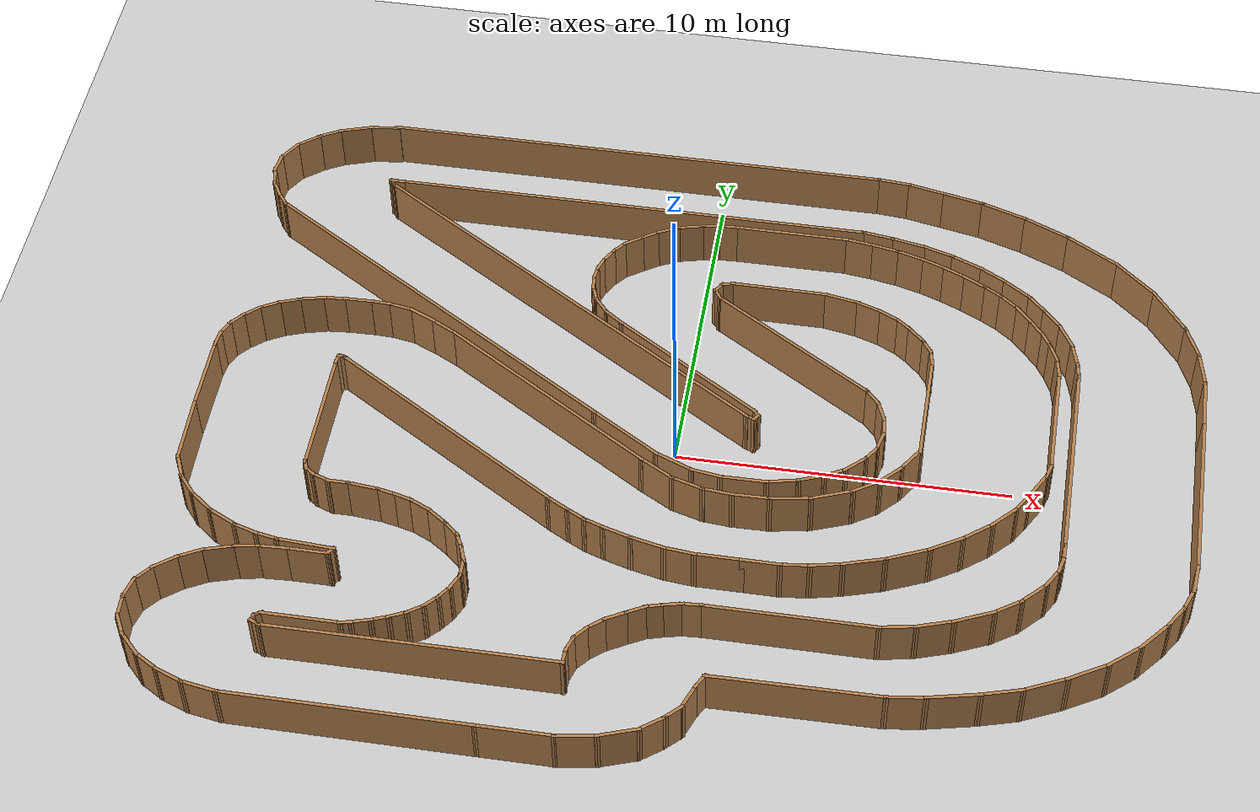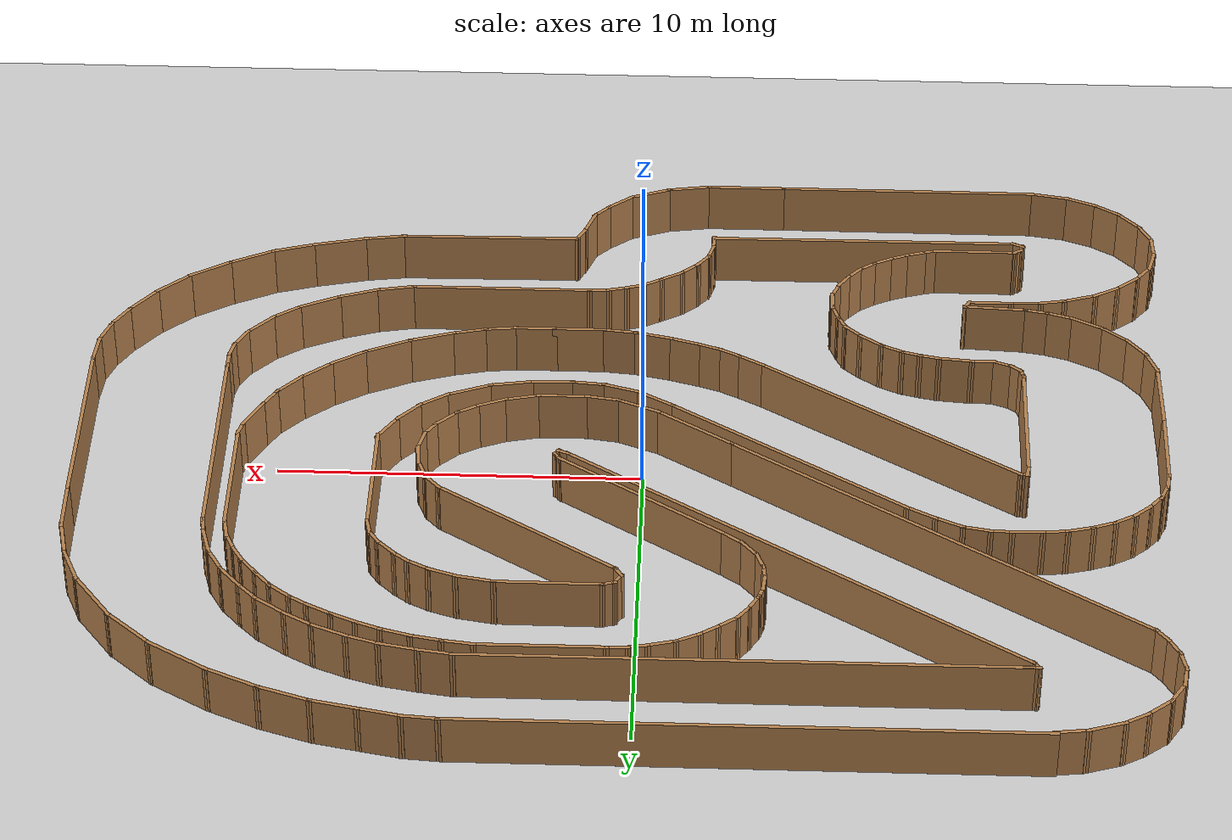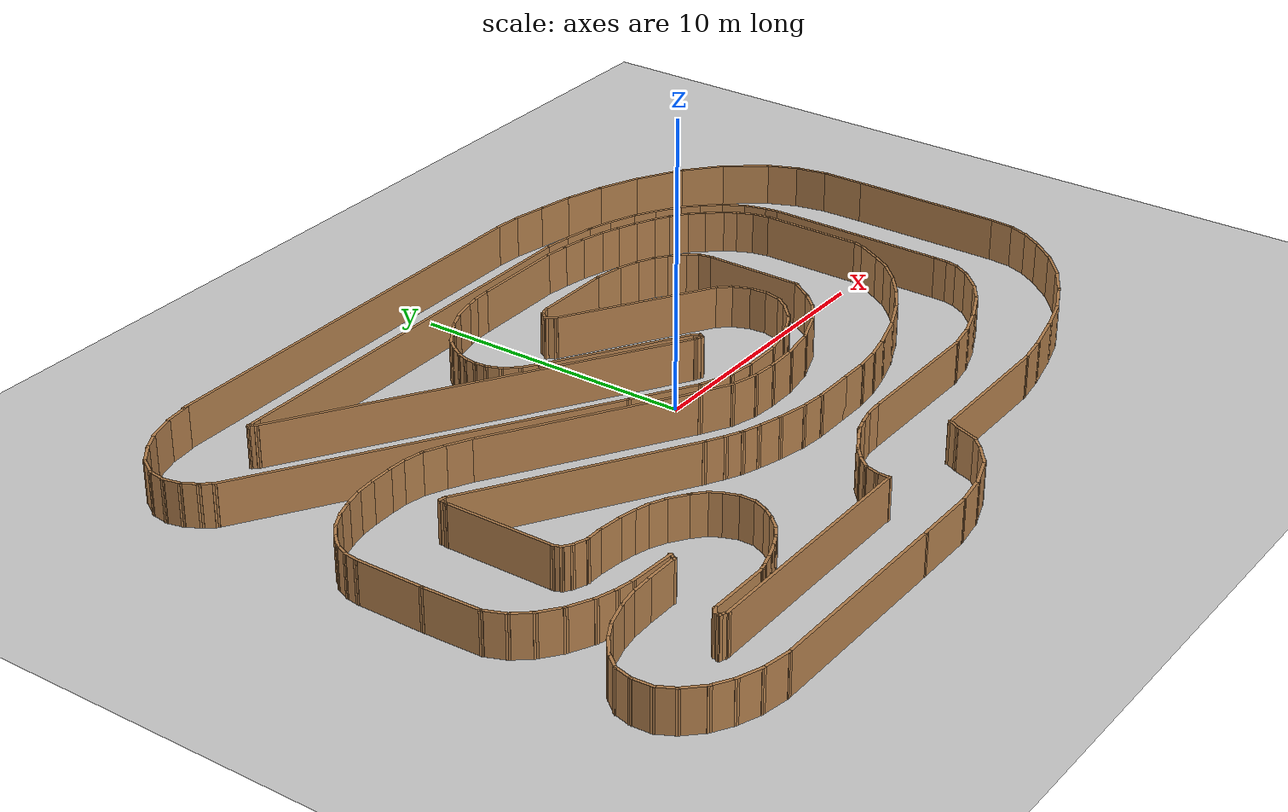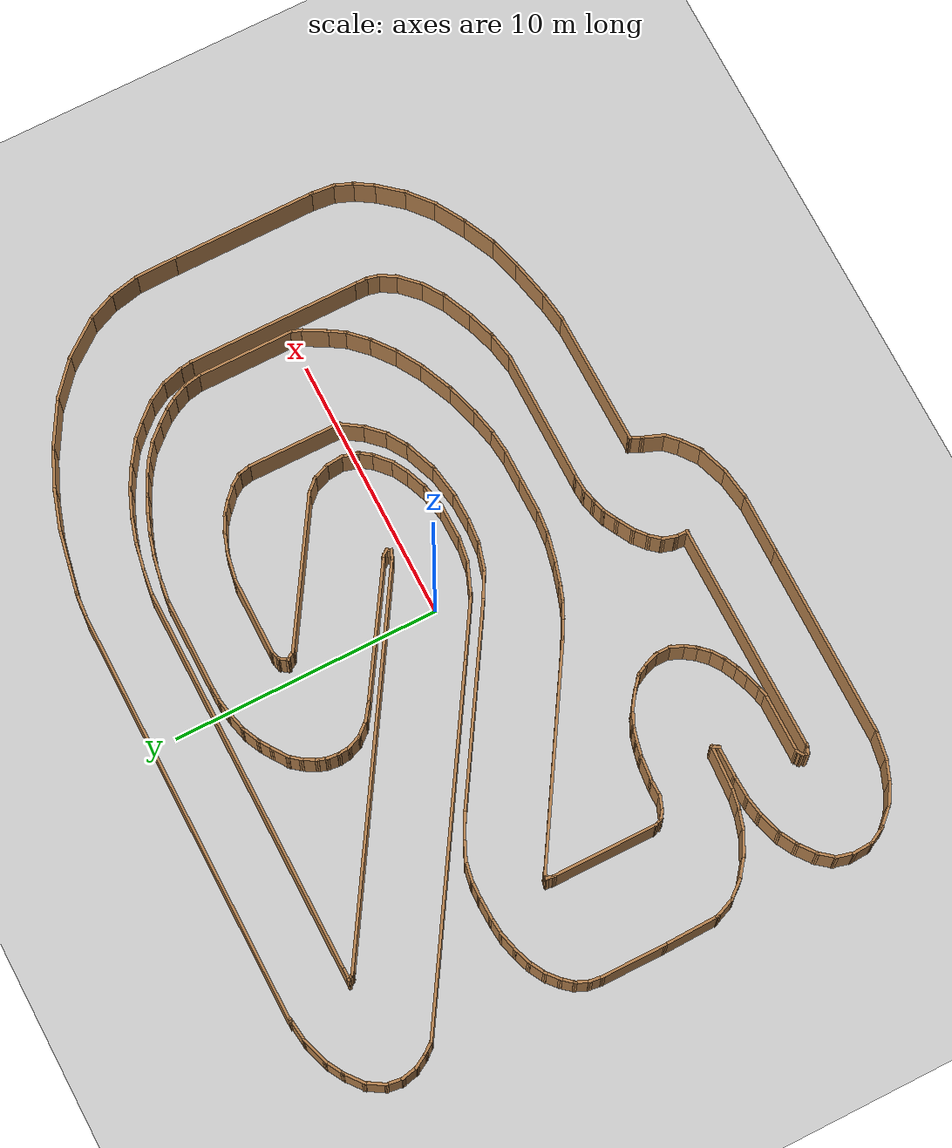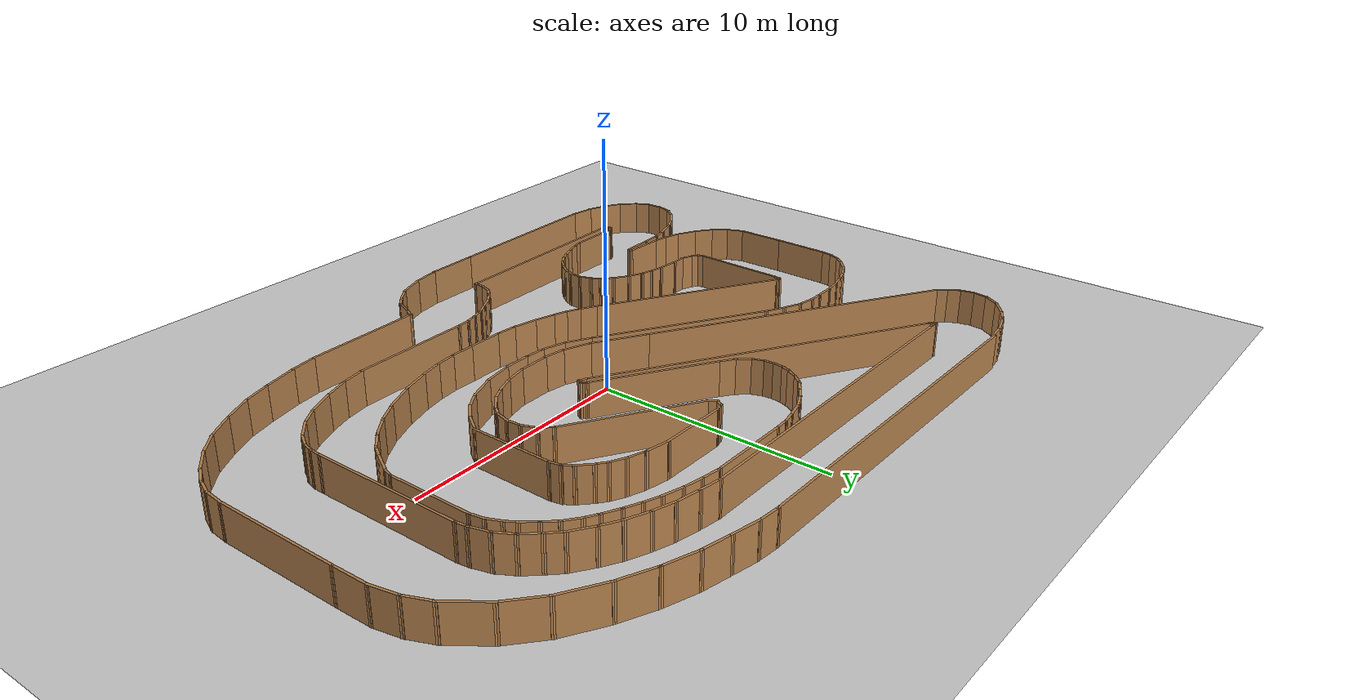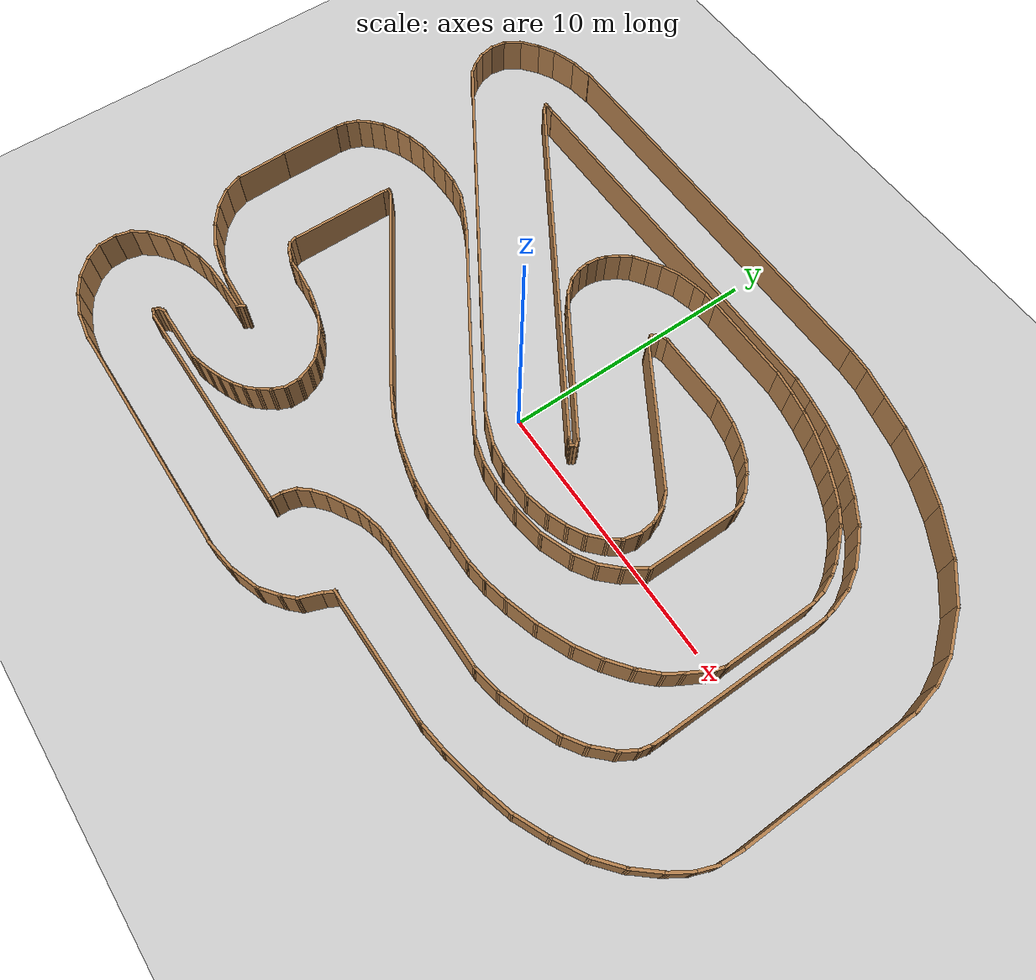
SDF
<?xml version="1.0" ?>
<sdf version="1.4">
  <!-- We use a custom world for the rrbot so that the camera angle is launched correctly -->

  <world name="default">

    <include>
      <uri>model://ground_plane</uri>
    </include>

    <include>
      <uri>model://rover_racetrack</uri>
    </include>

    <!-- Global light source -->
    <include>
      <uri>model://sun</uri>
    </include>

    <!-- Focus camera on tall pendulum -->
    <gui fullscreen='0'>
      <camera name='user_camera'>
        <pose>0.471107 3.112576 9.086079 0.000000 1.221795 -1.567757</pose>
        <view_controller>orbit</view_controller>
      </camera>
    </gui>

  </world>
</sdf>

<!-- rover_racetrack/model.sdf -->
<sdf version='1.6'>
  <model name='rover_racetrack'>
    <pose frame=''>0.515416 -0.136333 0 0 -0 0</pose>
    <link name='Wall_227'>
      <collision name='Wall_227_Collision'>
        <geometry>
          <box>
            <size>15.75 0.1 1.5</size>
          </box>
        </geometry>
        <pose frame=''>0 0 0.75 0 -0 0</pose>
      </collision>
      <visual name='Wall_227_Visual'>
        <pose frame=''>0 0 0.75 0 -0 0</pose>
        <geometry>
          <box>
            <size>15.75 0.1 1.5</size>
          </box>
        </geometry>
        <material>
          <script>
            <uri>file://media/materials/scripts/gazebo.material</uri>
            <name>Gazebo/Wood</name>
          </script>
          <ambient>1 1 1 1</ambient>
        </material>
      </visual>
      <pose frame=''>-3.4696 11.0332 0 0 -0 0</pose>
    </link>
    <link name='Wall_228'>
      <collision name='Wall_228_Collision'>
        <geometry>
          <box>
            <size>1.09613 0.1 1.5</size>
          </box>
        </geometry>
        <pose frame=''>0 0 0.75 0 -0 0</pose>
      </collision>
      <visual name='Wall_228_Visual'>
        <pose frame=''>0 0 0.75 0 -0 0</pose>
        <geometry>
          <box>
            <size>1.09613 0.1 1.5</size>
          </box>
        </geometry>
        <material>
          <script>
            <uri>file://media/materials/scripts/gazebo.material</uri>
            <name>Gazebo/Wood</name>
          </script>
          <ambient>1 1 1 1</ambient>
        </material>
      </visual>
      <pose frame=''>4.80197 10.9957 0 0 0 -0.079441</pose>
    </link>
    <link name='Wall_229'>
      <collision name='Wall_229_Collision'>
        <geometry>
          <box>
            <size>1.29854 0.1 1.5</size>
          </box>
        </geometry>
        <pose frame=''>0 0 0.75 0 -0 0</pose>
      </collision>
      <visual name='Wall_229_Visual'>
        <pose frame=''>0 0 0.75 0 -0 0</pose>
        <geometry>
          <box>
            <size>1.29854 0.1 1.5</size>
          </box>
        </geometry>
        <material>
          <script>
            <uri>file://media/materials/scripts/gazebo.material</uri>
            <name>Gazebo/Wood</name>
          </script>
          <ambient>1 1 1 1</ambient>
        </material>
      </visual>
      <pose frame=''>5.83666 10.8455 0 0 0 -0.197396</pose>
    </link>
    <link name='Wall_230'>
      <collision name='Wall_230_Collision'>
        <geometry>
          <box>
            <size>1.40162 0.1 1.5</size>
          </box>
        </geometry>
        <pose frame=''>0 0 0.75 0 -0 0</pose>
      </collision>
      <visual name='Wall_230_Visual'>
        <pose frame=''>0 0 0.75 0 -0 0</pose>
        <geometry>
          <box>
            <size>1.40162 0.1 1.5</size>
          </box>
        </geometry>
        <material>
          <script>
            <uri>file://media/materials/scripts/gazebo.material</uri>
            <name>Gazebo/Wood</name>
          </script>
          <ambient>1 1 1 1</ambient>
        </material>
      </visual>
      <pose frame=''>7.01295 10.6077 0 0 0 -0.201317</pose>
    </link>
    <link name='Wall_231'>
      <collision name='Wall_231_Collision'>
        <geometry>
          <box>
            <size>1.59835 0.1 1.5</size>
          </box>
        </geometry>
        <pose frame=''>0 0 0.75 0 -0 0</pose>
      </collision>
      <visual name='Wall_231_Visual'>
        <pose frame=''>0 0 0.75 0 -0 0</pose>
        <geometry>
          <box>
            <size>1.59835 0.1 1.5</size>
          </box>
        </geometry>
        <material>
          <script>
            <uri>file://media/materials/scripts/gazebo.material</uri>
            <name>Gazebo/Wood</name>
          </script>
          <ambient>1 1 1 1</ambient>
        </material>
      </visual>
      <pose frame=''>8.31438 10.2574 0 0 0 -0.316286</pose>
    </link>
    <link name='Wall_232'>
      <collision name='Wall_232_Collision'>
        <geometry>
          <box>
            <size>1.65186 0.1 1.5</size>
          </box>
        </geometry>
        <pose frame=''>0 0 0.75 0 -0 0</pose>
      </collision>
      <visual name='Wall_232_Visual'>
        <pose frame=''>0 0 0.75 0 -0 0</pose>
        <geometry>
          <box>
            <size>1.65186 0.1 1.5</size>
          </box>
        </geometry>
        <material>
          <script>
            <uri>file://media/materials/scripts/gazebo.material</uri>
            <name>Gazebo/Wood</name>
          </script>
          <ambient>1 1 1 1</ambient>
        </material>
      </visual>
      <pose frame=''>9.69089 9.73177 0 0 0 -0.411456</pose>
    </link>
    <link name='Wall_233'>
      <collision name='Wall_233_Collision'>
        <geometry>
          <box>
            <size>1.97855 0.1 1.5</size>
          </box>
        </geometry>
        <pose frame=''>0 0 0.75 0 -0 0</pose>
      </collision>
      <visual name='Wall_233_Visual'>
        <pose frame=''>0 0 0.75 0 -0 0</pose>
        <geometry>
          <box>
            <size>1.97855 0.1 1.5</size>
          </box>
        </geometry>
        <material>
          <script>
            <uri>file://media/materials/scripts/gazebo.material</uri>
            <name>Gazebo/Wood</name>
          </script>
          <ambient>1 1 1 1</ambient>
        </material>
      </visual>
      <pose frame=''>11.1675 8.96844 0 0 0 -0.53103</pose>
    </link>
    <link name='Wall_234'>
      <collision name='Wall_234_Collision'>
        <geometry>
          <box>
            <size>1.71096 0.1 1.5</size>
          </box>
        </geometry>
        <pose frame=''>0 0 0.75 0 -0 0</pose>
      </collision>
      <visual name='Wall_234_Visual'>
        <pose frame=''>0 0 0.75 0 -0 0</pose>
        <geometry>
          <box>
            <size>1.71096 0.1 1.5</size>
          </box>
        </geometry>
        <material>
          <script>
            <uri>file://media/materials/scripts/gazebo.material</uri>
            <name>Gazebo/Wood</name>
          </script>
          <ambient>1 1 1 1</ambient>
        </material>
      </visual>
      <pose frame=''>12.544 7.99237 0 0 0 -0.717322</pose>
    </link>
    <link name='Wall_235'>
      <collision name='Wall_235_Collision'>
        <geometry>
          <box>
            <size>1.81183 0.1 1.5</size>
          </box>
        </geometry>
        <pose frame=''>0 0 0.75 0 -0 0</pose>
      </collision>
      <visual name='Wall_235_Visual'>
        <pose frame=''>0 0 0.75 0 -0 0</pose>
        <geometry>
          <box>
            <size>1.81183 0.1 1.5</size>
          </box>
        </geometry>
        <material>
          <script>
            <uri>file://media/materials/scripts/gazebo.material</uri>
            <name>Gazebo/Wood</name>
          </script>
          <ambient>1 1 1 1</ambient>
        </material>
      </visual>
      <pose frame=''>13.6327 6.81607 0 0 0 -0.924283</pose>
    </link>
    <link name='Wall_236'>
      <collision name='Wall_236_Collision'>
        <geometry>
          <box>
            <size>1.21477 0.1 1.5</size>
          </box>
        </geometry>
        <pose frame=''>0 0 0.75 0 -0 0</pose>
      </collision>
      <visual name='Wall_236_Visual'>
        <pose frame=''>0 0 0.75 0 -0 0</pose>
        <geometry>
          <box>
            <size>1.21477 0.1 1.5</size>
          </box>
        </geometry>
        <material>
          <script>
            <uri>file://media/materials/scripts/gazebo.material</uri>
            <name>Gazebo/Wood</name>
          </script>
          <ambient>1 1 1 1</ambient>
        </material>
      </visual>
      <pose frame=''>14.346 5.66481 0 0 0 -1.15973</pose>
    </link>
    <link name='Wall_237'>
      <collision name='Wall_237_Collision'>
        <geometry>
          <box>
            <size>1.2495 0.1 1.5</size>
          </box>
        </geometry>
        <pose frame=''>0 0 0.75 0 -0 0</pose>
      </collision>
      <visual name='Wall_237_Visual'>
        <pose frame=''>0 0 0.75 0 -0 0</pose>
        <geometry>
          <box>
            <size>1.2495 0.1 1.5</size>
          </box>
        </geometry>
        <material>
          <script>
            <uri>file://media/materials/scripts/gazebo.material</uri>
            <name>Gazebo/Wood</name>
          </script>
          <ambient>1 1 1 1</ambient>
        </material>
      </visual>
      <pose frame=''>14.6714 4.63869 0 0 0 -1.36447</pose>
    </link>
    <link name='Wall_238'>
      <collision name='Wall_238_Collision'>
        <geometry>
          <box>
            <size>1.65186 0.1 1.5</size>
          </box>
        </geometry>
        <pose frame=''>0 0 0.75 0 -0 0</pose>
      </collision>
      <visual name='Wall_238_Visual'>
        <pose frame=''>0 0 0.75 0 -0 0</pose>
        <geometry>
          <box>
            <size>1.65186 0.1 1.5</size>
          </box>
        </geometry>
        <material>
          <script>
            <uri>file://media/materials/scripts/gazebo.material</uri>
            <name>Gazebo/Wood</name>
          </script>
          <ambient>1 1 1 1</ambient>
        </material>
      </visual>
      <pose frame=''>14.7965 3.34977 0 0 0 -1.55413</pose>
    </link>
    <link name='Wall_240'>
      <collision name='Wall_240_Collision'>
        <geometry>
          <box>
            <size>5.5 0.1 1.5</size>
          </box>
        </geometry>
        <pose frame=''>0 0 0.75 0 -0 0</pose>
      </collision>
      <visual name='Wall_240_Visual'>
        <pose frame=''>0 0 0.75 0 -0 0</pose>
        <geometry>
          <box>
            <size>5.5 0.1 1.5</size>
          </box>
        </geometry>
        <material>
          <script>
            <uri>file://media/materials/scripts/gazebo.material</uri>
            <name>Gazebo/Wood</name>
          </script>
          <ambient>1 1 1 1</ambient>
        </material>
      </visual>
      <pose frame=''>14.809 -0.07605 0 0 0 -1.5708</pose>
    </link>
    <link name='Wall_241'>
      <collision name='Wall_241_Collision'>
        <geometry>
          <box>
            <size>0.981868 0.1 1.5</size>
          </box>
        </geometry>
        <pose frame=''>0 0 0.75 0 -0 0</pose>
      </collision>
      <visual name='Wall_241_Visual'>
        <pose frame=''>0 0 0.75 0 -0 0</pose>
        <geometry>
          <box>
            <size>0.981868 0.1 1.5</size>
          </box>
        </geometry>
        <material>
          <script>
            <uri>file://media/materials/scripts/gazebo.material</uri>
            <name>Gazebo/Wood</name>
          </script>
          <ambient>1 1 1 1</ambient>
        </material>
      </visual>
      <pose frame=''>14.768 -3.16495 0 0 0 -1.66961</pose>
    </link>
    <link name='Wall_242'>
      <collision name='Wall_242_Collision'>
        <geometry>
          <box>
            <size>0.873436 0.1 1.5</size>
          </box>
        </geometry>
        <pose frame=''>0 0 0.75 0 -0 0</pose>
      </collision>
      <visual name='Wall_242_Visual'>
        <pose frame=''>0 0 0.75 0 -0 0</pose>
        <geometry>
          <box>
            <size>0.873436 0.1 1.5</size>
          </box>
        </geometry>
        <material>
          <script>
            <uri>file://media/materials/scripts/gazebo.material</uri>
            <name>Gazebo/Wood</name>
          </script>
          <ambient>1 1 1 1</ambient>
        </material>
      </visual>
      <pose frame=''>14.5964 -3.91619 0 0 0 -1.94013</pose>
    </link>
    <link name='Wall_243'>
      <collision name='Wall_243_Collision'>
        <geometry>
          <box>
            <size>0.922816 0.1 1.5</size>
          </box>
        </geometry>
        <pose frame=''>0 0 0.75 0 -0 0</pose>
      </collision>
      <visual name='Wall_243_Visual'>
        <pose frame=''>0 0 0.75 0 -0 0</pose>
        <geometry>
          <box>
            <size>0.922816 0.1 1.5</size>
          </box>
        </geometry>
        <material>
          <script>
            <uri>file://media/materials/scripts/gazebo.material</uri>
            <name>Gazebo/Wood</name>
          </script>
          <ambient>1 1 1 1</ambient>
        </material>
      </visual>
      <pose frame=''>14.259 -4.57996 0 0 0 -2.13537</pose>
    </link>
    <link name='Wall_245'>
      <collision name='Wall_245_Collision'>
        <geometry>
          <box>
            <size>1.24319 0.1 1.5</size>
          </box>
        </geometry>
        <pose frame=''>0 0 0.75 0 -0 0</pose>
      </collision>
      <visual name='Wall_245_Visual'>
        <pose frame=''>0 0 0.75 0 -0 0</pose>
        <geometry>
          <box>
            <size>1.24319 0.1 1.5</size>
          </box>
        </geometry>
        <material>
          <script>
            <uri>file://media/materials/scripts/gazebo.material</uri>
            <name>Gazebo/Wood</name>
          </script>
          <ambient>1 1 1 1</ambient>
        </material>
      </visual>
      <pose frame=''>13.7008 -5.325 0 0 0 -2.26926</pose>
    </link>
    <link name='Wall_246'>
      <collision name='Wall_246_Collision'>
        <geometry>
          <box>
            <size>1.26842 0.1 1.5</size>
          </box>
        </geometry>
        <pose frame=''>0 0 0.75 0 -0 0</pose>
      </collision>
      <visual name='Wall_246_Visual'>
        <pose frame=''>0 0 0.75 0 -0 0</pose>
        <geometry>
          <box>
            <size>1.26842 0.1 1.5</size>
          </box>
        </geometry>
        <material>
          <script>
            <uri>file://media/materials/scripts/gazebo.material</uri>
            <name>Gazebo/Wood</name>
          </script>
          <ambient>1 1 1 1</ambient>
        </material>
      </visual>
      <pose frame=''>12.9239 -6.1065 0 0 0 -2.43539</pose>
    </link>
    <link name='Wall_247'>
      <collision name='Wall_247_Collision'>
        <geometry>
          <box>
            <size>1.39485 0.1 1.5</size>
          </box>
        </geometry>
        <pose frame=''>0 0 0.75 0 -0 0</pose>
      </collision>
      <visual name='Wall_247_Visual'>
        <pose frame=''>0 0 0.75 0 -0 0</pose>
        <geometry>
          <box>
            <size>1.39485 0.1 1.5</size>
          </box>
        </geometry>
        <material>
          <script>
            <uri>file://media/materials/scripts/gazebo.material</uri>
            <name>Gazebo/Wood</name>
          </script>
          <ambient>1 1 1 1</ambient>
        </material>
      </visual>
      <pose frame=''>11.9603 -6.78224 0 0 0 -2.61497</pose>
    </link>
    <link name='Wall_248'>
      <collision name='Wall_248_Collision'>
        <geometry>
          <box>
            <size>1.44878 0.1 1.5</size>
          </box>
        </geometry>
        <pose frame=''>0 0 0.75 0 -0 0</pose>
      </collision>
      <visual name='Wall_248_Visual'>
        <pose frame=''>0 0 0.75 0 -0 0</pose>
        <geometry>
          <box>
            <size>1.44878 0.1 1.5</size>
          </box>
        </geometry>
        <material>
          <script>
            <uri>file://media/materials/scripts/gazebo.material</uri>
            <name>Gazebo/Wood</name>
          </script>
          <ambient>1 1 1 1</ambient>
        </material>
      </visual>
      <pose frame=''>10.8341 -7.37039 0 0 0 -2.7038</pose>
    </link>
    <link name='Wall_249'>
      <collision name='Wall_249_Collision'>
        <geometry>
          <box>
            <size>1.32229 0.1 1.5</size>
          </box>
        </geometry>
        <pose frame=''>0 0 0.75 0 -0 0</pose>
      </collision>
      <visual name='Wall_249_Visual'>
        <pose frame=''>0 0 0.75 0 -0 0</pose>
        <geometry>
          <box>
            <size>1.32229 0.1 1.5</size>
          </box>
        </geometry>
        <material>
          <script>
            <uri>file://media/materials/scripts/gazebo.material</uri>
            <name>Gazebo/Wood</name>
          </script>
          <ambient>1 1 1 1</ambient>
        </material>
      </visual>
      <pose frame=''>9.6828 -7.80837 0 0 0 -2.86036</pose>
    </link>
    <link name='Wall_250'>
      <collision name='Wall_250_Collision'>
        <geometry>
          <box>
            <size>1.63761 0.1 1.5</size>
          </box>
        </geometry>
        <pose frame=''>0 0 0.75 0 -0 0</pose>
      </collision>
      <visual name='Wall_250_Visual'>
        <pose frame=''>0 0 0.75 0 -0 0</pose>
        <geometry>
          <box>
            <size>1.63761 0.1 1.5</size>
          </box>
        </geometry>
        <material>
          <script>
            <uri>file://media/materials/scripts/gazebo.material</uri>
            <name>Gazebo/Wood</name>
          </script>
          <ambient>1 1 1 1</ambient>
        </material>
      </visual>
      <pose frame=''>8.39388 -8.13373 0 0 0 -2.9211</pose>
    </link>
    <link name='Wall_251'>
      <collision name='Wall_251_Collision'>
        <geometry>
          <box>
            <size>1.23661 0.1 1.5</size>
          </box>
        </geometry>
        <pose frame=''>0 0 0.75 0 -0 0</pose>
      </collision>
      <visual name='Wall_251_Visual'>
        <pose frame=''>0 0 0.75 0 -0 0</pose>
        <geometry>
          <box>
            <size>1.23661 0.1 1.5</size>
          </box>
        </geometry>
        <material>
          <script>
            <uri>file://media/materials/scripts/gazebo.material</uri>
            <name>Gazebo/Wood</name>
          </script>
          <ambient>1 1 1 1</ambient>
        </material>
      </visual>
      <pose frame=''>7.13 -8.37149 0 0 0 -3.00295</pose>
    </link>
    <link name='Wall_252'>
      <collision name='Wall_252_Collision'>
        <geometry>
          <box>
            <size>5.10569 0.1 1.5</size>
          </box>
        </geometry>
        <pose frame=''>0 0 0.75 0 -0 0</pose>
      </collision>
      <visual name='Wall_252_Visual'>
        <pose frame=''>0 0 0.75 0 -0 0</pose>
        <geometry>
          <box>
            <size>5.10569 0.1 1.5</size>
          </box>
        </geometry>
        <material>
          <script>
            <uri>file://media/materials/scripts/gazebo.material</uri>
            <name>Gazebo/Wood</name>
          </script>
          <ambient>1 1 1 1</ambient>
        </material>
      </visual>
      <pose frame=''>4.11419 -8.4716 0 0 0 -3.13149</pose>
    </link>
    <link name='Wall_253'>
      <collision name='Wall_253_Collision'>
        <geometry>
          <box>
            <size>0.575467 0.1 1.5</size>
          </box>
        </geometry>
        <pose frame=''>0 0 0.75 0 -0 0</pose>
      </collision>
      <visual name='Wall_253_Visual'>
        <pose frame=''>0 0 0.75 0 -0 0</pose>
        <geometry>
          <box>
            <size>0.575467 0.1 1.5</size>
          </box>
        </geometry>
        <material>
          <script>
            <uri>file://media/materials/scripts/gazebo.material</uri>
            <name>Gazebo/Wood</name>
          </script>
          <ambient>1 1 1 1</ambient>
        </material>
      </visual>
      <pose frame=''>1.53636 -8.68433 0 0 0 -2.06075</pose>
    </link>
    <link name='Wall_254'>
      <collision name='Wall_254_Collision'>
        <geometry>
          <box>
            <size>0.926255 0.1 1.5</size>
          </box>
        </geometry>
        <pose frame=''>0 0 0.75 0 -0 0</pose>
      </collision>
      <visual name='Wall_254_Visual'>
        <pose frame=''>0 0 0.75 0 -0 0</pose>
        <geometry>
          <box>
            <size>0.926255 0.1 1.5</size>
          </box>
        </geometry>
        <material>
          <script>
            <uri>file://media/materials/scripts/gazebo.material</uri>
            <name>Gazebo/Wood</name>
          </script>
          <ambient>1 1 1 1</ambient>
        </material>
      </visual>
      <pose frame=''>1.2986 -9.23493 0 0 0 -1.93334</pose>
    </link>
    <link name='Wall_255'>
      <collision name='Wall_255_Collision'>
        <geometry>
          <box>
            <size>0.716307 0.1 1.5</size>
          </box>
        </geometry>
        <pose frame=''>0 0 0.75 0 -0 0</pose>
      </collision>
      <visual name='Wall_255_Visual'>
        <pose frame=''>0 0 0.75 0 -0 0</pose>
        <geometry>
          <box>
            <size>0.716307 0.1 1.5</size>
          </box>
        </geometry>
        <material>
          <script>
            <uri>file://media/materials/scripts/gazebo.material</uri>
            <name>Gazebo/Wood</name>
          </script>
          <ambient>1 1 1 1</ambient>
        </material>
      </visual>
      <pose frame=''>0.960729 -9.79805 0 0 0 -2.35619</pose>
    </link>
    <link name='Wall_259'>
      <collision name='Wall_259_Collision'>
        <geometry>
          <box>
            <size>0.942505 0.1 1.5</size>
          </box>
        </geometry>
        <pose frame=''>0 0 0.75 0 -0 0</pose>
      </collision>
      <visual name='Wall_259_Visual'>
        <pose frame=''>0 0 0.75 0 -0 0</pose>
        <geometry>
          <box>
            <size>0.942505 0.1 1.5</size>
          </box>
        </geometry>
        <material>
          <script>
            <uri>file://media/materials/scripts/gazebo.material</uri>
            <name>Gazebo/Wood</name>
          </script>
          <ambient>1 1 1 1</ambient>
        </material>
      </visual>
      <pose frame=''>0.445868 -10.2391 0 0 0 -2.48823</pose>
    </link>
    <link name='Wall_260'>
      <collision name='Wall_260_Collision'>
        <geometry>
          <box>
            <size>1.29316 0.1 1.5</size>
          </box>
        </geometry>
        <pose frame=''>0 0 0.75 0 -0 0</pose>
      </collision>
      <visual name='Wall_260_Visual'>
        <pose frame=''>0 0 0.75 0 -0 0</pose>
        <geometry>
          <box>
            <size>1.29316 0.1 1.5</size>
          </box>
        </geometry>
        <material>
          <script>
            <uri>file://media/materials/scripts/gazebo.material</uri>
            <name>Gazebo/Wood</name>
          </script>
          <ambient>1 1 1 1</ambient>
        </material>
      </visual>
      <pose frame=''>-0.408117 -10.6692 0 0 0 -2.80414</pose>
    </link>
    <link name='Wall_261'>
      <collision name='Wall_261_Collision'>
        <geometry>
          <box>
            <size>1.29816 0.1 1.5</size>
          </box>
        </geometry>
        <pose frame=''>0 0 0.75 0 -0 0</pose>
      </collision>
      <visual name='Wall_261_Visual'>
        <pose frame=''>0 0 0.75 0 -0 0</pose>
        <geometry>
          <box>
            <size>1.29816 0.1 1.5</size>
          </box>
        </geometry>
        <material>
          <script>
            <uri>file://media/materials/scripts/gazebo.material</uri>
            <name>Gazebo/Wood</name>
          </script>
          <ambient>1 1 1 1</ambient>
        </material>
      </visual>
      <pose frame=''>-1.51544 -10.9436 0 0 0 -2.99289</pose>
    </link>
    <link name='Wall_262'>
      <collision name='Wall_262_Collision'>
        <geometry>
          <box>
            <size>2.295 0.1 1.5</size>
          </box>
        </geometry>
        <pose frame=''>0 0 0.75 0 -0 0</pose>
      </collision>
      <visual name='Wall_262_Visual'>
        <pose frame=''>0 0 0.75 0 -0 0</pose>
        <geometry>
          <box>
            <size>2.295 0.1 1.5</size>
          </box>
        </geometry>
        <material>
          <script>
            <uri>file://media/materials/scripts/gazebo.material</uri>
            <name>Gazebo/Wood</name>
          </script>
          <ambient>1 1 1 1</ambient>
        </material>
      </visual>
      <pose frame=''>-3.18092 -11.0287 0 0 -0 3.14159</pose>
    </link>
    <link name='Wall_263'>
      <collision name='Wall_263_Collision'>
        <geometry>
          <box>
            <size>7.30343 0.1 1.5</size>
          </box>
        </geometry>
        <pose frame=''>0 0 0.75 0 -0 0</pose>
      </collision>
      <visual name='Wall_263_Visual'>
        <pose frame=''>0 0 0.75 0 -0 0</pose>
        <geometry>
          <box>
            <size>7.30343 0.1 1.5</size>
          </box>
        </geometry>
        <material>
          <script>
            <uri>file://media/materials/scripts/gazebo.material</uri>
            <name>Gazebo/Wood</name>
          </script>
          <ambient>1 1 1 1</ambient>
        </material>
      </visual>
      <pose frame=''>-7.85498 -11.0193 0 0 -0 3.13897</pose>
    </link>
    <link name='Wall_264'>
      <collision name='Wall_264_Collision'>
        <geometry>
          <box>
            <size>1.16735 0.1 1.5</size>
          </box>
        </geometry>
        <pose frame=''>0 0 0.75 0 -0 0</pose>
      </collision>
      <visual name='Wall_264_Visual'>
        <pose frame=''>0 0 0.75 0 -0 0</pose>
        <geometry>
          <box>
            <size>1.16735 0.1 1.5</size>
          </box>
        </geometry>
        <material>
          <script>
            <uri>file://media/materials/scripts/gazebo.material</uri>
            <name>Gazebo/Wood</name>
          </script>
          <ambient>1 1 1 1</ambient>
        </material>
      </visual>
      <pose frame=''>-11.933 -10.9247 0 0 -0 2.97339</pose>
    </link>
    <link name='Wall_265'>
      <collision name='Wall_265_Collision'>
        <geometry>
          <box>
            <size>1.00054 0.1 1.5</size>
          </box>
        </geometry>
        <pose frame=''>0 0 0.75 0 -0 0</pose>
      </collision>
      <visual name='Wall_265_Visual'>
        <pose frame=''>0 0 0.75 0 -0 0</pose>
        <geometry>
          <box>
            <size>1.00054 0.1 1.5</size>
          </box>
        </geometry>
        <material>
          <script>
            <uri>file://media/materials/scripts/gazebo.material</uri>
            <name>Gazebo/Wood</name>
          </script>
          <ambient>1 1 1 1</ambient>
        </material>
      </visual>
      <pose frame=''>-12.832 -10.6882 0 0 -0 2.77761</pose>
    </link>
    <link name='Wall_266'>
      <collision name='Wall_266_Collision'>
        <geometry>
          <box>
            <size>0.922429 0.1 1.5</size>
          </box>
        </geometry>
        <pose frame=''>0 0 0.75 0 -0 0</pose>
      </collision>
      <visual name='Wall_266_Visual'>
        <pose frame=''>0 0 0.75 0 -0 0</pose>
        <geometry>
          <box>
            <size>0.922429 0.1 1.5</size>
          </box>
        </geometry>
        <material>
          <script>
            <uri>file://media/materials/scripts/gazebo.material</uri>
            <name>Gazebo/Wood</name>
          </script>
          <ambient>1 1 1 1</ambient>
        </material>
      </visual>
      <pose frame=''>-13.5605 -10.3381 0 0 -0 2.60117</pose>
    </link>
    <link name='Wall_268'>
      <collision name='Wall_268_Collision'>
        <geometry>
          <box>
            <size>0.966383 0.1 1.5</size>
          </box>
        </geometry>
        <pose frame=''>0 0 0.75 0 -0 0</pose>
      </collision>
      <visual name='Wall_268_Visual'>
        <pose frame=''>0 0 0.75 0 -0 0</pose>
        <geometry>
          <box>
            <size>0.966383 0.1 1.5</size>
          </box>
        </geometry>
        <material>
          <script>
            <uri>file://media/materials/scripts/gazebo.material</uri>
            <name>Gazebo/Wood</name>
          </script>
          <ambient>1 1 1 1</ambient>
        </material>
      </visual>
      <pose frame=''>-14.1756 -9.84604 0 0 -0 2.3398</pose>
    </link>
    <link name='Wall_269'>
      <collision name='Wall_269_Collision'>
        <geometry>
          <box>
            <size>0.793428 0.1 1.5</size>
          </box>
        </geometry>
        <pose frame=''>0 0 0.75 0 -0 0</pose>
      </collision>
      <visual name='Wall_269_Visual'>
        <pose frame=''>0 0 0.75 0 -0 0</pose>
        <geometry>
          <box>
            <size>0.793428 0.1 1.5</size>
          </box>
        </geometry>
        <material>
          <script>
            <uri>file://media/materials/scripts/gazebo.material</uri>
            <name>Gazebo/Wood</name>
          </script>
          <ambient>1 1 1 1</ambient>
        </material>
      </visual>
      <pose frame=''>-14.6108 -9.26885 0 0 -0 2.06075</pose>
    </link>
    <link name='Wall_270'>
      <collision name='Wall_270_Collision'>
        <geometry>
          <box>
            <size>0.832327 0.1 1.5</size>
          </box>
        </geometry>
        <pose frame=''>0 0 0.75 0 -0 0</pose>
      </collision>
      <visual name='Wall_270_Visual'>
        <pose frame=''>0 0 0.75 0 -0 0</pose>
        <geometry>
          <box>
            <size>0.832327 0.1 1.5</size>
          </box>
        </geometry>
        <material>
          <script>
            <uri>file://media/materials/scripts/gazebo.material</uri>
            <name>Gazebo/Wood</name>
          </script>
          <ambient>1 1 1 1</ambient>
        </material>
      </visual>
      <pose frame=''>-14.7812 -8.64434 0 0 -0 1.6263</pose>
    </link>
    <link name='Wall_271'>
      <collision name='Wall_271_Collision'>
        <geometry>
          <box>
            <size>0.774217 0.1 1.5</size>
          </box>
        </geometry>
        <pose frame=''>0 0 0.75 0 -0 0</pose>
      </collision>
      <visual name='Wall_271_Visual'>
        <pose frame=''>0 0 0.75 0 -0 0</pose>
        <geometry>
          <box>
            <size>0.774217 0.1 1.5</size>
          </box>
        </geometry>
        <material>
          <script>
            <uri>file://media/materials/scripts/gazebo.material</uri>
            <name>Gazebo/Wood</name>
          </script>
          <ambient>1 1 1 1</ambient>
        </material>
      </visual>
      <pose frame=''>-14.7244 -8.00092 0 0 -0 1.32582</pose>
    </link>
    <link name='Wall_272'>
      <collision name='Wall_272_Collision'>
        <geometry>
          <box>
            <size>0.782481 0.1 1.5</size>
          </box>
        </geometry>
        <pose frame=''>0 0 0.75 0 -0 0</pose>
      </collision>
      <visual name='Wall_272_Visual'>
        <pose frame=''>0 0 0.75 0 -0 0</pose>
        <geometry>
          <box>
            <size>0.782481 0.1 1.5</size>
          </box>
        </geometry>
        <material>
          <script>
            <uri>file://media/materials/scripts/gazebo.material</uri>
            <name>Gazebo/Wood</name>
          </script>
          <ambient>1 1 1 1</ambient>
        </material>
      </visual>
      <pose frame=''>-14.45 -7.45211 0 0 -0 0.891383</pose>
    </link>
    <link name='Wall_273'>
      <collision name='Wall_273_Collision'>
        <geometry>
          <box>
            <size>0.891921 0.1 1.5</size>
          </box>
        </geometry>
        <pose frame=''>0 0 0.75 0 -0 0</pose>
      </collision>
      <visual name='Wall_273_Visual'>
        <pose frame=''>0 0 0.75 0 -0 0</pose>
        <geometry>
          <box>
            <size>0.891921 0.1 1.5</size>
          </box>
        </geometry>
        <material>
          <script>
            <uri>file://media/materials/scripts/gazebo.material</uri>
            <name>Gazebo/Wood</name>
          </script>
          <ambient>1 1 1 1</ambient>
        </material>
      </visual>
      <pose frame=''>-13.958 -6.979 0 0 -0 0.658806</pose>
    </link>
    <link name='Wall_274'>
      <collision name='Wall_274_Collision'>
        <geometry>
          <box>
            <size>0.861364 0.1 1.5</size>
          </box>
        </geometry>
        <pose frame=''>0 0 0.75 0 -0 0</pose>
      </collision>
      <visual name='Wall_274_Visual'>
        <pose frame=''>0 0 0.75 0 -0 0</pose>
        <geometry>
          <box>
            <size>0.861364 0.1 1.5</size>
          </box>
        </geometry>
        <material>
          <script>
            <uri>file://media/materials/scripts/gazebo.material</uri>
            <name>Gazebo/Wood</name>
          </script>
          <ambient>1 1 1 1</ambient>
        </material>
      </visual>
      <pose frame=''>-13.3524 -6.58159 0 0 -0 0.499347</pose>
    </link>
    <link name='Wall_275'>
      <collision name='Wall_275_Collision'>
        <geometry>
          <box>
            <size>1.05994 0.1 1.5</size>
          </box>
        </geometry>
        <pose frame=''>0 0 0.75 0 -0 0</pose>
      </collision>
      <visual name='Wall_275_Visual'>
        <pose frame=''>0 0 0.75 0 -0 0</pose>
        <geometry>
          <box>
            <size>1.05994 0.1 1.5</size>
          </box>
        </geometry>
        <material>
          <script>
            <uri>file://media/materials/scripts/gazebo.material</uri>
            <name>Gazebo/Wood</name>
          </script>
          <ambient>1 1 1 1</ambient>
        </material>
      </visual>
      <pose frame=''>-12.6049 -6.2788 0 0 -0 0.295441</pose>
    </link>
    <link name='Wall_276'>
      <collision name='Wall_276_Collision'>
        <geometry>
          <box>
            <size>0.822014 0.1 1.5</size>
          </box>
        </geometry>
        <pose frame=''>0 0 0.75 0 -0 0</pose>
      </collision>
      <visual name='Wall_276_Visual'>
        <pose frame=''>0 0 0.75 0 -0 0</pose>
        <geometry>
          <box>
            <size>0.822014 0.1 1.5</size>
          </box>
        </geometry>
        <material>
          <script>
            <uri>file://media/materials/scripts/gazebo.material</uri>
            <name>Gazebo/Wood</name>
          </script>
          <ambient>1 1 1 1</ambient>
        </material>
      </visual>
      <pose frame=''>-11.8384 -6.08956 0 0 -0 0.169778</pose>
    </link>
    <link name='Wall_277'>
      <collision name='Wall_277_Collision'>
        <geometry>
          <box>
            <size>0.983531 0.1 1.5</size>
          </box>
        </geometry>
        <pose frame=''>0 0 0.75 0 -0 0</pose>
      </collision>
      <visual name='Wall_277_Visual'>
        <pose frame=''>0 0 0.75 0 -0 0</pose>
        <geometry>
          <box>
            <size>0.983531 0.1 1.5</size>
          </box>
        </geometry>
        <material>
          <script>
            <uri>file://media/materials/scripts/gazebo.material</uri>
            <name>Gazebo/Wood</name>
          </script>
          <ambient>1 1 1 1</ambient>
        </material>
      </visual>
      <pose frame=''>-11.0909 -6.01386 0 0 -0 0.045423</pose>
    </link>
    <link name='Wall_278'>
      <collision name='Wall_278_Collision'>
        <geometry>
          <box>
            <size>1.32331 0.1 1.5</size>
          </box>
        </geometry>
        <pose frame=''>0 0 0.75 0 -0 0</pose>
      </collision>
      <visual name='Wall_278_Visual'>
        <pose frame=''>0 0 0.75 0 -0 0</pose>
        <geometry>
          <box>
            <size>1.32331 0.1 1.5</size>
          </box>
        </geometry>
        <material>
          <script>
            <uri>file://media/materials/scripts/gazebo.material</uri>
            <name>Gazebo/Wood</name>
          </script>
          <ambient>1 1 1 1</ambient>
        </material>
      </visual>
      <pose frame=''>-10.0879 -5.99493 0 0 -0 0</pose>
    </link>
    <link name='Wall_279'>
      <collision name='Wall_279_Collision'>
        <geometry>
          <box>
            <size>0.370694 0.1 1.5</size>
          </box>
        </geometry>
        <pose frame=''>0 0 0.75 0 -0 0</pose>
      </collision>
      <visual name='Wall_279_Visual'>
        <pose frame=''>0 0 0.75 0 -0 0</pose>
        <geometry>
          <box>
            <size>0.370694 0.1 1.5</size>
          </box>
        </geometry>
        <material>
          <script>
            <uri>file://media/materials/scripts/gazebo.material</uri>
            <name>Gazebo/Wood</name>
          </script>
          <ambient>1 1 1 1</ambient>
        </material>
      </visual>
      <pose frame=''>-9.44449 -5.90031 0 0 -0 1.03038</pose>
    </link>
    <link name='Wall_280'>
      <collision name='Wall_280_Collision'>
        <geometry>
          <box>
            <size>1.81706 0.1 1.5</size>
          </box>
        </geometry>
        <pose frame=''>0 0 0.75 0 -0 0</pose>
      </collision>
      <visual name='Wall_280_Visual'>
        <pose frame=''>0 0 0.75 0 -0 0</pose>
        <geometry>
          <box>
            <size>1.81706 0.1 1.5</size>
          </box>
        </geometry>
        <material>
          <script>
            <uri>file://media/materials/scripts/gazebo.material</uri>
            <name>Gazebo/Wood</name>
          </script>
          <ambient>1 1 1 1</ambient>
        </material>
      </visual>
      <pose frame=''>-10.2204 -5.75838 0 0 -0 3.08483</pose>
    </link>
    <link name='Wall_281'>
      <collision name='Wall_281_Collision'>
        <geometry>
          <box>
            <size>0.784742 0.1 1.5</size>
          </box>
        </geometry>
        <pose frame=''>0 0 0.75 0 -0 0</pose>
      </collision>
      <visual name='Wall_281_Visual'>
        <pose frame=''>0 0 0.75 0 -0 0</pose>
        <geometry>
          <box>
            <size>0.784742 0.1 1.5</size>
          </box>
        </geometry>
        <material>
          <script>
            <uri>file://media/materials/scripts/gazebo.material</uri>
            <name>Gazebo/Wood</name>
          </script>
          <ambient>1 1 1 1</ambient>
        </material>
      </visual>
      <pose frame=''>-11.3653 -5.6543 0 0 -0 2.96174</pose>
    </link>
    <link name='Wall_282'>
      <collision name='Wall_282_Collision'>
        <geometry>
          <box>
            <size>0.86237 0.1 1.5</size>
          </box>
        </geometry>
        <pose frame=''>0 0 0.75 0 -0 0</pose>
      </collision>
      <visual name='Wall_282_Visual'>
        <pose frame=''>0 0 0.75 0 -0 0</pose>
        <geometry>
          <box>
            <size>0.86237 0.1 1.5</size>
          </box>
        </geometry>
        <material>
          <script>
            <uri>file://media/materials/scripts/gazebo.material</uri>
            <name>Gazebo/Wood</name>
          </script>
          <ambient>1 1 1 1</ambient>
        </material>
      </visual>
      <pose frame=''>-12.0182 -5.49344 0 0 -0 2.84505</pose>
    </link>
    <link name='Wall_284'>
      <collision name='Wall_284_Collision'>
        <geometry>
          <box>
            <size>1.08096 0.1 1.5</size>
          </box>
        </geometry>
        <pose frame=''>0 0 0.75 0 -0 0</pose>
      </collision>
      <visual name='Wall_284_Visual'>
        <pose frame=''>0 0 0.75 0 -0 0</pose>
        <geometry>
          <box>
            <size>1.08096 0.1 1.5</size>
          </box>
        </geometry>
        <material>
          <script>
            <uri>file://media/materials/scripts/gazebo.material</uri>
            <name>Gazebo/Wood</name>
          </script>
          <ambient>1 1 1 1</ambient>
        </material>
      </visual>
      <pose frame=''>-12.7752 -5.18119 0 0 -0 2.67794</pose>
    </link>
    <link name='Wall_285'>
      <collision name='Wall_285_Collision'>
        <geometry>
          <box>
            <size>0.986533 0.1 1.5</size>
          </box>
        </geometry>
        <pose frame=''>0 0 0.75 0 -0 0</pose>
      </collision>
      <visual name='Wall_285_Visual'>
        <pose frame=''>0 0 0.75 0 -0 0</pose>
        <geometry>
          <box>
            <size>0.986533 0.1 1.5</size>
          </box>
        </geometry>
        <material>
          <script>
            <uri>file://media/materials/scripts/gazebo.material</uri>
            <name>Gazebo/Wood</name>
          </script>
          <ambient>1 1 1 1</ambient>
        </material>
      </visual>
      <pose frame=''>-13.5227 -4.71754 0 0 -0 2.48452</pose>
    </link>
    <link name='Wall_286'>
      <collision name='Wall_286_Collision'>
        <geometry>
          <box>
            <size>0.889019 0.1 1.5</size>
          </box>
        </geometry>
        <pose frame=''>0 0 0.75 0 -0 0</pose>
      </collision>
      <visual name='Wall_286_Visual'>
        <pose frame=''>0 0 0.75 0 -0 0</pose>
        <geometry>
          <box>
            <size>0.889019 0.1 1.5</size>
          </box>
        </geometry>
        <material>
          <script>
            <uri>file://media/materials/scripts/gazebo.material</uri>
            <name>Gazebo/Wood</name>
          </script>
          <ambient>1 1 1 1</ambient>
        </material>
      </visual>
      <pose frame=''>-14.0904 -4.1782 0 0 -0 2.26553</pose>
    </link>
    <link name='Wall_287'>
      <collision name='Wall_287_Collision'>
        <geometry>
          <box>
            <size>0.88805 0.1 1.5</size>
          </box>
        </geometry>
        <pose frame=''>0 0 0.75 0 -0 0</pose>
      </collision>
      <visual name='Wall_287_Visual'>
        <pose frame=''>0 0 0.75 0 -0 0</pose>
        <geometry>
          <box>
            <size>0.88805 0.1 1.5</size>
          </box>
        </geometry>
        <material>
          <script>
            <uri>file://media/materials/scripts/gazebo.material</uri>
            <name>Gazebo/Wood</name>
          </script>
          <ambient>1 1 1 1</ambient>
        </material>
      </visual>
      <pose frame=''>-14.4689 -3.55369 0 0 -0 1.96559</pose>
    </link>
    <link name='Wall_288'>
      <collision name='Wall_288_Collision'>
        <geometry>
          <box>
            <size>2.1757 0.1 1.5</size>
          </box>
        </geometry>
        <pose frame=''>0 0 0.75 0 -0 0</pose>
      </collision>
      <visual name='Wall_288_Visual'>
        <pose frame=''>0 0 0.75 0 -0 0</pose>
        <geometry>
          <box>
            <size>2.1757 0.1 1.5</size>
          </box>
        </geometry>
        <material>
          <script>
            <uri>file://media/materials/scripts/gazebo.material</uri>
            <name>Gazebo/Wood</name>
          </script>
          <ambient>1 1 1 1</ambient>
        </material>
      </visual>
      <pose frame=''>-14.6392 -2.2006 0 0 -0 1.59883</pose>
    </link>
    <link name='Wall_290'>
      <collision name='Wall_290_Collision'>
        <geometry>
          <box>
            <size>2.5 0.1 1.5</size>
          </box>
        </geometry>
        <pose frame=''>0 0 0.75 0 -0 0</pose>
      </collision>
      <visual name='Wall_290_Visual'>
        <pose frame=''>0 0 0.75 0 -0 0</pose>
        <geometry>
          <box>
            <size>2.5 0.1 1.5</size>
          </box>
        </geometry>
        <material>
          <script>
            <uri>file://media/materials/scripts/gazebo.material</uri>
            <name>Gazebo/Wood</name>
          </script>
          <ambient>1 1 1 1</ambient>
        </material>
      </visual>
      <pose frame=''>-14.6676 -0.01315 0 0 -0 1.5708</pose>
    </link>
    <link name='Wall_291'>
      <collision name='Wall_291_Collision'>
        <geometry>
          <box>
            <size>0.585595 0.1 1.5</size>
          </box>
        </geometry>
        <pose frame=''>0 0 0.75 0 -0 0</pose>
      </collision>
      <visual name='Wall_291_Visual'>
        <pose frame=''>0 0 0.75 0 -0 0</pose>
        <geometry>
          <box>
            <size>0.585595 0.1 1.5</size>
          </box>
        </geometry>
        <material>
          <script>
            <uri>file://media/materials/scripts/gazebo.material</uri>
            <name>Gazebo/Wood</name>
          </script>
          <ambient>1 1 1 1</ambient>
        </material>
      </visual>
      <pose frame=''>-14.6392 1.37779 0 0 -0 1.44009</pose>
    </link>
    <link name='Wall_292'>
      <collision name='Wall_292_Collision'>
        <geometry>
          <box>
            <size>0.642033 0.1 1.5</size>
          </box>
        </geometry>
        <pose frame=''>0 0 0.75 0 -0 0</pose>
      </collision>
      <visual name='Wall_292_Visual'>
        <pose frame=''>0 0 0.75 0 -0 0</pose>
        <geometry>
          <box>
            <size>0.642033 0.1 1.5</size>
          </box>
        </geometry>
        <material>
          <script>
            <uri>file://media/materials/scripts/gazebo.material</uri>
            <name>Gazebo/Wood</name>
          </script>
          <ambient>1 1 1 1</ambient>
        </material>
      </visual>
      <pose frame=''>-14.5162 1.82082 0 0 -0 1.176</pose>
    </link>
    <link name='Wall_293'>
      <collision name='Wall_293_Collision'>
        <geometry>
          <box>
            <size>0.646742 0.1 1.5</size>
          </box>
        </geometry>
        <pose frame=''>0 0 0.75 0 -0 0</pose>
      </collision>
      <visual name='Wall_293_Visual'>
        <pose frame=''>0 0 0.75 0 -0 0</pose>
        <geometry>
          <box>
            <size>0.646742 0.1 1.5</size>
          </box>
        </geometry>
        <material>
          <script>
            <uri>file://media/materials/scripts/gazebo.material</uri>
            <name>Gazebo/Wood</name>
          </script>
          <ambient>1 1 1 1</ambient>
        </material>
      </visual>
      <pose frame=''>-14.2607 2.23716 0 0 -0 0.866302</pose>
    </link>
    <link name='Wall_294'>
      <collision name='Wall_294_Collision'>
        <geometry>
          <box>
            <size>0.70011 0.1 1.5</size>
          </box>
        </geometry>
        <pose frame=''>0 0 0.75 0 -0 0</pose>
      </collision>
      <visual name='Wall_294_Visual'>
        <pose frame=''>0 0 0.75 0 -0 0</pose>
        <geometry>
          <box>
            <size>0.70011 0.1 1.5</size>
          </box>
        </geometry>
        <material>
          <script>
            <uri>file://media/materials/scripts/gazebo.material</uri>
            <name>Gazebo/Wood</name>
          </script>
          <ambient>1 1 1 1</ambient>
        </material>
      </visual>
      <pose frame=''>-13.8917 2.60618 0 0 -0 0.712358</pose>
    </link>
    <link name='Wall_295'>
      <collision name='Wall_295_Collision'>
        <geometry>
          <box>
            <size>0.776793 0.1 1.5</size>
          </box>
        </geometry>
        <pose frame=''>0 0 0.75 0 -0 0</pose>
      </collision>
      <visual name='Wall_295_Visual'>
        <pose frame=''>0 0 0.75 0 -0 0</pose>
        <geometry>
          <box>
            <size>0.776793 0.1 1.5</size>
          </box>
        </geometry>
        <material>
          <script>
            <uri>file://media/materials/scripts/gazebo.material</uri>
            <name>Gazebo/Wood</name>
          </script>
          <ambient>1 1 1 1</ambient>
        </material>
      </visual>
      <pose frame=''>-13.4091 2.93736 0 0 -0 0.504166</pose>
    </link>
    <link name='Wall_296'>
      <collision name='Wall_296_Collision'>
        <geometry>
          <box>
            <size>0.772493 0.1 1.5</size>
          </box>
        </geometry>
        <pose frame=''>0 0 0.75 0 -0 0</pose>
      </collision>
      <visual name='Wall_296_Visual'>
        <pose frame=''>0 0 0.75 0 -0 0</pose>
        <geometry>
          <box>
            <size>0.772493 0.1 1.5</size>
          </box>
        </geometry>
        <material>
          <script>
            <uri>file://media/materials/scripts/gazebo.material</uri>
            <name>Gazebo/Wood</name>
          </script>
          <ambient>1 1 1 1</ambient>
        </material>
      </visual>
      <pose frame=''>-12.8414 3.19284 0 0 -0 0.340979</pose>
    </link>
    <link name='Wall_297'>
      <collision name='Wall_297_Collision'>
        <geometry>
          <box>
            <size>0.852244 0.1 1.5</size>
          </box>
        </geometry>
        <pose frame=''>0 0 0.75 0 -0 0</pose>
      </collision>
      <visual name='Wall_297_Visual'>
        <pose frame=''>0 0 0.75 0 -0 0</pose>
        <geometry>
          <box>
            <size>0.852244 0.1 1.5</size>
          </box>
        </geometry>
        <material>
          <script>
            <uri>file://media/materials/scripts/gazebo.material</uri>
            <name>Gazebo/Wood</name>
          </script>
          <ambient>1 1 1 1</ambient>
        </material>
      </visual>
      <pose frame=''>-12.2074 3.38208 0 0 -0 0.244979</pose>
    </link>
    <link name='Wall_298'>
      <collision name='Wall_298_Collision'>
        <geometry>
          <box>
            <size>0.814781 0.1 1.5</size>
          </box>
        </geometry>
        <pose frame=''>0 0 0.75 0 -0 0</pose>
      </collision>
      <visual name='Wall_298_Visual'>
        <pose frame=''>0 0 0.75 0 -0 0</pose>
        <geometry>
          <box>
            <size>0.814781 0.1 1.5</size>
          </box>
        </geometry>
        <material>
          <script>
            <uri>file://media/materials/scripts/gazebo.material</uri>
            <name>Gazebo/Wood</name>
          </script>
          <ambient>1 1 1 1</ambient>
        </material>
      </visual>
      <pose frame=''>-11.5356 3.49563 0 0 -0 0.085505</pose>
    </link>
    <link name='Wall_299'>
      <collision name='Wall_299_Collision'>
        <geometry>
          <box>
            <size>0.963967 0.1 1.5</size>
          </box>
        </geometry>
        <pose frame=''>0 0 0.75 0 -0 0</pose>
      </collision>
      <visual name='Wall_299_Visual'>
        <pose frame=''>0 0 0.75 0 -0 0</pose>
        <geometry>
          <box>
            <size>0.963967 0.1 1.5</size>
          </box>
        </geometry>
        <material>
          <script>
            <uri>file://media/materials/scripts/gazebo.material</uri>
            <name>Gazebo/Wood</name>
          </script>
          <ambient>1 1 1 1</ambient>
        </material>
      </visual>
      <pose frame=''>-10.7976 3.53348 0 0 -0 0.023252</pose>
    </link>
    <link name='Wall_300'>
      <collision name='Wall_300_Collision'>
        <geometry>
          <box>
            <size>0.718991 0.1 1.5</size>
          </box>
        </geometry>
        <pose frame=''>0 0 0.75 0 -0 0</pose>
      </collision>
      <visual name='Wall_300_Visual'>
        <pose frame=''>0 0 0.75 0 -0 0</pose>
        <geometry>
          <box>
            <size>0.718991 0.1 1.5</size>
          </box>
        </geometry>
        <material>
          <script>
            <uri>file://media/materials/scripts/gazebo.material</uri>
            <name>Gazebo/Wood</name>
          </script>
          <ambient>1 1 1 1</ambient>
        </material>
      </visual>
      <pose frame=''>-10.1068 3.53348 0 0 0 -0.033321</pose>
    </link>
    <link name='Wall_301'>
      <collision name='Wall_301_Collision'>
        <geometry>
          <box>
            <size>0.881225 0.1 1.5</size>
          </box>
        </geometry>
        <pose frame=''>0 0 0.75 0 -0 0</pose>
      </collision>
      <visual name='Wall_301_Visual'>
        <pose frame=''>0 0 0.75 0 -0 0</pose>
        <geometry>
          <box>
            <size>0.881225 0.1 1.5</size>
          </box>
        </geometry>
        <material>
          <script>
            <uri>file://media/materials/scripts/gazebo.material</uri>
            <name>Gazebo/Wood</name>
          </script>
          <ambient>1 1 1 1</ambient>
        </material>
      </visual>
      <pose frame=''>-9.46342 3.45778 0 0 0 -0.182168</pose>
    </link>
    <link name='Wall_302'>
      <collision name='Wall_302_Collision'>
        <geometry>
          <box>
            <size>0.937808 0.1 1.5</size>
          </box>
        </geometry>
        <pose frame=''>0 0 0.75 0 -0 0</pose>
      </collision>
      <visual name='Wall_302_Visual'>
        <pose frame=''>0 0 0.75 0 -0 0</pose>
        <geometry>
          <box>
            <size>0.937808 0.1 1.5</size>
          </box>
        </geometry>
        <material>
          <script>
            <uri>file://media/materials/scripts/gazebo.material</uri>
            <name>Gazebo/Wood</name>
          </script>
          <ambient>1 1 1 1</ambient>
        </material>
      </visual>
      <pose frame=''>-8.74429 3.23069 0 0 0 -0.420663</pose>
    </link>
    <link name='Wall_303'>
      <collision name='Wall_303_Collision'>
        <geometry>
          <box>
            <size>1.00495 0.1 1.5</size>
          </box>
        </geometry>
        <pose frame=''>0 0 0.75 0 -0 0</pose>
      </collision>
      <visual name='Wall_303_Visual'>
        <pose frame=''>0 0 0.75 0 -0 0</pose>
        <geometry>
          <box>
            <size>1.00495 0.1 1.5</size>
          </box>
        </geometry>
        <material>
          <script>
            <uri>file://media/materials/scripts/gazebo.material</uri>
            <name>Gazebo/Wood</name>
          </script>
          <ambient>1 1 1 1</ambient>
        </material>
      </visual>
      <pose frame=''>-8.00624 2.87112 0 0 0 -0.483447</pose>
    </link>
    <link name='Wall_304'>
      <collision name='Wall_304_Collision'>
        <geometry>
          <box>
            <size>7.62227 0.1 1.5</size>
          </box>
        </geometry>
        <pose frame=''>0 0 0.75 0 -0 0</pose>
      </collision>
      <visual name='Wall_304_Visual'>
        <pose frame=''>0 0 0.75 0 -0 0</pose>
        <geometry>
          <box>
            <size>7.62227 0.1 1.5</size>
          </box>
        </geometry>
        <material>
          <script>
            <uri>file://media/materials/scripts/gazebo.material</uri>
            <name>Gazebo/Wood</name>
          </script>
          <ambient>1 1 1 1</ambient>
        </material>
      </visual>
      <pose frame=''>-4.45793 0.694823 0 0 0 -0.557794</pose>
    </link>
    <link name='Wall_305'>
      <collision name='Wall_305_Collision'>
        <geometry>
          <box>
            <size>1.27675 0.1 1.5</size>
          </box>
        </geometry>
        <pose frame=''>0 0 0.75 0 -0 0</pose>
      </collision>
      <visual name='Wall_305_Visual'>
        <pose frame=''>0 0 0.75 0 -0 0</pose>
        <geometry>
          <box>
            <size>1.27675 0.1 1.5</size>
          </box>
        </geometry>
        <material>
          <script>
            <uri>file://media/materials/scripts/gazebo.material</uri>
            <name>Gazebo/Wood</name>
          </script>
          <ambient>1 1 1 1</ambient>
        </material>
      </visual>
      <pose frame=''>-0.796067 -1.55717 0 0 0 -0.50873</pose>
    </link>
    <link name='Wall_306'>
      <collision name='Wall_306_Collision'>
        <geometry>
          <box>
            <size>1.1144 0.1 1.5</size>
          </box>
        </geometry>
        <pose frame=''>0 0 0.75 0 -0 0</pose>
      </collision>
      <visual name='Wall_306_Visual'>
        <pose frame=''>0 0 0.75 0 -0 0</pose>
        <geometry>
          <box>
            <size>1.1144 0.1 1.5</size>
          </box>
        </geometry>
        <material>
          <script>
            <uri>file://media/materials/scripts/gazebo.material</uri>
            <name>Gazebo/Wood</name>
          </script>
          <ambient>1 1 1 1</ambient>
        </material>
      </visual>
      <pose frame=''>0.159613 -1.96405 0 0 0 -0.2783</pose>
    </link>
    <link name='Wall_307'>
      <collision name='Wall_307_Collision'>
        <geometry>
          <box>
            <size>1.02381 0.1 1.5</size>
          </box>
        </geometry>
        <pose frame=''>0 0 0.75 0 -0 0</pose>
      </collision>
      <visual name='Wall_307_Visual'>
        <pose frame=''>0 0 0.75 0 -0 0</pose>
        <geometry>
          <box>
            <size>1.02381 0.1 1.5</size>
          </box>
        </geometry>
        <material>
          <script>
            <uri>file://media/materials/scripts/gazebo.material</uri>
            <name>Gazebo/Wood</name>
          </script>
          <ambient>1 1 1 1</ambient>
        </material>
      </visual>
      <pose frame=''>1.05852 -2.13437 0 0 0 -0.086738</pose>
    </link>
    <link name='Wall_308'>
      <collision name='Wall_308_Collision'>
        <geometry>
          <box>
            <size>1.22885 0.1 1.5</size>
          </box>
        </geometry>
        <pose frame=''>0 0 0.75 0 -0 0</pose>
      </collision>
      <visual name='Wall_308_Visual'>
        <pose frame=''>0 0 0.75 0 -0 0</pose>
        <geometry>
          <box>
            <size>1.22885 0.1 1.5</size>
          </box>
        </geometry>
        <material>
          <script>
            <uri>file://media/materials/scripts/gazebo.material</uri>
            <name>Gazebo/Wood</name>
          </script>
          <ambient>1 1 1 1</ambient>
        </material>
      </visual>
      <pose frame=''>2.03312 -2.16275 0 0 -0 0.017542</pose>
    </link>
    <link name='Wall_310'>
      <collision name='Wall_310_Collision'>
        <geometry>
          <box>
            <size>1.33847 0.1 1.5</size>
          </box>
        </geometry>
        <pose frame=''>0 0 0.75 0 -0 0</pose>
      </collision>
      <visual name='Wall_310_Visual'>
        <pose frame=''>0 0 0.75 0 -0 0</pose>
        <geometry>
          <box>
            <size>1.33847 0.1 1.5</size>
          </box>
        </geometry>
        <material>
          <script>
            <uri>file://media/materials/scripts/gazebo.material</uri>
            <name>Gazebo/Wood</name>
          </script>
          <ambient>1 1 1 1</ambient>
        </material>
      </visual>
      <pose frame=''>3.15912 -2.05867 0 0 -0 0.159913</pose>
    </link>
    <link name='Wall_311'>
      <collision name='Wall_311_Collision'>
        <geometry>
          <box>
            <size>1.38372 0.1 1.5</size>
          </box>
        </geometry>
        <pose frame=''>0 0 0.75 0 -0 0</pose>
      </collision>
      <visual name='Wall_311_Visual'>
        <pose frame=''>0 0 0.75 0 -0 0</pose>
        <geometry>
          <box>
            <size>1.38372 0.1 1.5</size>
          </box>
        </geometry>
        <material>
          <script>
            <uri>file://media/materials/scripts/gazebo.material</uri>
            <name>Gazebo/Wood</name>
          </script>
          <ambient>1 1 1 1</ambient>
        </material>
      </visual>
      <pose frame=''>4.32297 -1.74642 0 0 -0 0.360566</pose>
    </link>
    <link name='Wall_312'>
      <collision name='Wall_312_Collision'>
        <geometry>
          <box>
            <size>1.00054 0.1 1.5</size>
          </box>
        </geometry>
        <pose frame=''>0 0 0.75 0 -0 0</pose>
      </collision>
      <visual name='Wall_312_Visual'>
        <pose frame=''>0 0 0.75 0 -0 0</pose>
        <geometry>
          <box>
            <size>1.00054 0.1 1.5</size>
          </box>
        </geometry>
        <material>
          <script>
            <uri>file://media/materials/scripts/gazebo.material</uri>
            <name>Gazebo/Wood</name>
          </script>
          <ambient>1 1 1 1</ambient>
        </material>
      </visual>
      <pose frame=''>5.25973 -1.3017 0 0 -0 0.563316</pose>
    </link>
    <link name='Wall_313'>
      <collision name='Wall_313_Collision'>
        <geometry>
          <box>
            <size>0.966383 0.1 1.5</size>
          </box>
        </geometry>
        <pose frame=''>0 0 0.75 0 -0 0</pose>
      </collision>
      <visual name='Wall_313_Visual'>
        <pose frame=''>0 0 0.75 0 -0 0</pose>
        <geometry>
          <box>
            <size>0.966383 0.1 1.5</size>
          </box>
        </geometry>
        <material>
          <script>
            <uri>file://media/materials/scripts/gazebo.material</uri>
            <name>Gazebo/Wood</name>
          </script>
          <ambient>1 1 1 1</ambient>
        </material>
      </visual>
      <pose frame=''>5.90315 -0.781276 0 0 -0 0.80179</pose>
    </link>
    <link name='Wall_314'>
      <collision name='Wall_314_Collision'>
        <geometry>
          <box>
            <size>1.03712 0.1 1.5</size>
          </box>
        </geometry>
        <pose frame=''>0 0 0.75 0 -0 0</pose>
      </collision>
      <visual name='Wall_314_Visual'>
        <pose frame=''>0 0 0.75 0 -0 0</pose>
        <geometry>
          <box>
            <size>1.03712 0.1 1.5</size>
          </box>
        </geometry>
        <material>
          <script>
            <uri>file://media/materials/scripts/gazebo.material</uri>
            <name>Gazebo/Wood</name>
          </script>
          <ambient>1 1 1 1</ambient>
        </material>
      </visual>
      <pose frame=''>6.43304 -0.11887 0 0 -0 0.982861</pose>
    </link>
    <link name='Wall_315'>
      <collision name='Wall_315_Collision'>
        <geometry>
          <box>
            <size>3.57536 0.1 1.5</size>
          </box>
        </geometry>
        <pose frame=''>0 0 0.75 0 -0 0</pose>
      </collision>
      <visual name='Wall_315_Visual'>
        <pose frame=''>0 0 0.75 0 -0 0</pose>
        <geometry>
          <box>
            <size>3.57536 0.1 1.5</size>
          </box>
        </geometry>
        <material>
          <script>
            <uri>file://media/materials/scripts/gazebo.material</uri>
            <name>Gazebo/Wood</name>
          </script>
          <ambient>1 1 1 1</ambient>
        </material>
      </visual>
      <pose frame=''>6.68851 1.95335 0 0 -0 1.56527</pose>
    </link>
    <link name='Wall_316'>
      <collision name='Wall_316_Collision'>
        <geometry>
          <box>
            <size>0.595321 0.1 1.5</size>
          </box>
        </geometry>
        <pose frame=''>0 0 0.75 0 -0 0</pose>
      </collision>
      <visual name='Wall_316_Visual'>
        <pose frame=''>0 0 0.75 0 -0 0</pose>
        <geometry>
          <box>
            <size>0.595321 0.1 1.5</size>
          </box>
        </geometry>
        <material>
          <script>
            <uri>file://media/materials/scripts/gazebo.material</uri>
            <name>Gazebo/Wood</name>
          </script>
          <ambient>1 1 1 1</ambient>
        </material>
      </visual>
      <pose frame=''>6.65067 3.89309 0 0 -0 1.78491</pose>
    </link>
    <link name='Wall_317'>
      <collision name='Wall_317_Collision'>
        <geometry>
          <box>
            <size>0.585671 0.1 1.5</size>
          </box>
        </geometry>
        <pose frame=''>0 0 0.75 0 -0 0</pose>
      </collision>
      <visual name='Wall_317_Visual'>
        <pose frame=''>0 0 0.75 0 -0 0</pose>
        <geometry>
          <box>
            <size>0.585671 0.1 1.5</size>
          </box>
        </geometry>
        <material>
          <script>
            <uri>file://media/materials/scripts/gazebo.material</uri>
            <name>Gazebo/Wood</name>
          </script>
          <ambient>1 1 1 1</ambient>
        </material>
      </visual>
      <pose frame=''>6.48035 4.29045 0 0 -0 2.17085</pose>
    </link>
    <link name='Wall_318'>
      <collision name='Wall_318_Collision'>
        <geometry>
          <box>
            <size>0.805832 0.1 1.5</size>
          </box>
        </geometry>
        <pose frame=''>0 0 0.75 0 -0 0</pose>
      </collision>
      <visual name='Wall_318_Visual'>
        <pose frame=''>0 0 0.75 0 -0 0</pose>
        <geometry>
          <box>
            <size>0.805832 0.1 1.5</size>
          </box>
        </geometry>
        <material>
          <script>
            <uri>file://media/materials/scripts/gazebo.material</uri>
            <name>Gazebo/Wood</name>
          </script>
          <ambient>1 1 1 1</ambient>
        </material>
      </visual>
      <pose frame=''>6.12078 4.69732 0 0 -0 2.3766</pose>
    </link>
    <link name='Wall_320'>
      <collision name='Wall_320_Collision'>
        <geometry>
          <box>
            <size>0.610205 0.1 1.5</size>
          </box>
        </geometry>
        <pose frame=''>0 0 0.75 0 -0 0</pose>
      </collision>
      <visual name='Wall_320_Visual'>
        <pose frame=''>0 0 0.75 0 -0 0</pose>
        <geometry>
          <box>
            <size>0.610205 0.1 1.5</size>
          </box>
        </geometry>
        <material>
          <script>
            <uri>file://media/materials/scripts/gazebo.material</uri>
            <name>Gazebo/Wood</name>
          </script>
          <ambient>1 1 1 1</ambient>
        </material>
      </visual>
      <pose frame=''>5.70129 5.06398 0 0 -0 2.48988</pose>
    </link>
    <link name='Wall_321'>
      <collision name='Wall_321_Collision'>
        <geometry>
          <box>
            <size>0.786592 0.1 1.5</size>
          </box>
        </geometry>
        <pose frame=''>0 0 0.75 0 -0 0</pose>
      </collision>
      <visual name='Wall_321_Visual'>
        <pose frame=''>0 0 0.75 0 -0 0</pose>
        <geometry>
          <box>
            <size>0.786592 0.1 1.5</size>
          </box>
        </geometry>
        <material>
          <script>
            <uri>file://media/materials/scripts/gazebo.material</uri>
            <name>Gazebo/Wood</name>
          </script>
          <ambient>1 1 1 1</ambient>
        </material>
      </visual>
      <pose frame=''>5.23448 5.34754 0 0 -0 2.67217</pose>
    </link>
    <link name='Wall_322'>
      <collision name='Wall_322_Collision'>
        <geometry>
          <box>
            <size>0.922773 0.1 1.5</size>
          </box>
        </geometry>
        <pose frame=''>0 0 0.75 0 -0 0</pose>
      </collision>
      <visual name='Wall_322_Visual'>
        <pose frame=''>0 0 0.75 0 -0 0</pose>
        <geometry>
          <box>
            <size>0.922773 0.1 1.5</size>
          </box>
        </geometry>
        <material>
          <script>
            <uri>file://media/materials/scripts/gazebo.material</uri>
            <name>Gazebo/Wood</name>
          </script>
          <ambient>1 1 1 1</ambient>
        </material>
      </visual>
      <pose frame=''>4.58447 5.61495 0 0 -0 2.81648</pose>
    </link>
    <link name='Wall_323'>
      <collision name='Wall_323_Collision'>
        <geometry>
          <box>
            <size>1.17 0.1 1.5</size>
          </box>
        </geometry>
        <pose frame=''>0 0 0.75 0 -0 0</pose>
      </collision>
      <visual name='Wall_323_Visual'>
        <pose frame=''>0 0 0.75 0 -0 0</pose>
        <geometry>
          <box>
            <size>1.17 0.1 1.5</size>
          </box>
        </geometry>
        <material>
          <script>
            <uri>file://media/materials/scripts/gazebo.material</uri>
            <name>Gazebo/Wood</name>
          </script>
          <ambient>1 1 1 1</ambient>
        </material>
      </visual>
      <pose frame=''>3.71642 5.82888 0 0 -0 2.96318</pose>
    </link>
    <link name='Wall_324'>
      <collision name='Wall_324_Collision'>
        <geometry>
          <box>
            <size>2.9887 0.1 1.5</size>
          </box>
        </geometry>
        <pose frame=''>0 0 0.75 0 -0 0</pose>
      </collision>
      <visual name='Wall_324_Visual'>
        <pose frame=''>0 0 0.75 0 -0 0</pose>
        <geometry>
          <box>
            <size>2.9887 0.1 1.5</size>
          </box>
        </geometry>
        <material>
          <script>
            <uri>file://media/materials/scripts/gazebo.material</uri>
            <name>Gazebo/Wood</name>
          </script>
          <ambient>1 1 1 1</ambient>
        </material>
      </visual>
      <pose frame=''>1.79518 5.92761 0 0 -0 3.1358</pose>
    </link>
    <link name='Wall_325'>
      <collision name='Wall_325_Collision'>
        <geometry>
          <box>
            <size>0.483411 0.1 1.5</size>
          </box>
        </geometry>
        <pose frame=''>0 0 0.75 0 -0 0</pose>
      </collision>
      <visual name='Wall_325_Visual'>
        <pose frame=''>0 0 0.75 0 -0 0</pose>
        <geometry>
          <box>
            <size>0.483411 0.1 1.5</size>
          </box>
        </geometry>
        <material>
          <script>
            <uri>file://media/materials/scripts/gazebo.material</uri>
            <name>Gazebo/Wood</name>
          </script>
          <ambient>1 1 1 1</ambient>
        </material>
      </visual>
      <pose frame=''>0.215412 5.89059 0 0 0 -2.86668</pose>
    </link>
    <link name='Wall_326'>
      <collision name='Wall_326_Collision'>
        <geometry>
          <box>
            <size>0.471839 0.1 1.5</size>
          </box>
        </geometry>
        <pose frame=''>0 0 0.75 0 -0 0</pose>
      </collision>
      <visual name='Wall_326_Visual'>
        <pose frame=''>0 0 0.75 0 -0 0</pose>
        <geometry>
          <box>
            <size>0.471839 0.1 1.5</size>
          </box>
        </geometry>
        <material>
          <script>
            <uri>file://media/materials/scripts/gazebo.material</uri>
            <name>Gazebo/Wood</name>
          </script>
          <ambient>1 1 1 1</ambient>
        </material>
      </visual>
      <pose frame=''>-0.031427 5.70957 0 0 0 -2.13753</pose>
    </link>
    <link name='Wall_327'>
      <collision name='Wall_327_Collision'>
        <geometry>
          <box>
            <size>0.464928 0.1 1.5</size>
          </box>
        </geometry>
        <pose frame=''>0 0 0.75 0 -0 0</pose>
      </collision>
      <visual name='Wall_327_Visual'>
        <pose frame=''>0 0 0.75 0 -0 0</pose>
        <geometry>
          <box>
            <size>0.464928 0.1 1.5</size>
          </box>
        </geometry>
        <material>
          <script>
            <uri>file://media/materials/scripts/gazebo.material</uri>
            <name>Gazebo/Wood</name>
          </script>
          <ambient>1 1 1 1</ambient>
        </material>
      </visual>
      <pose frame=''>-0.031427 5.44216 0 0 0 -0.99004</pose>
    </link>
    <link name='Wall_330'>
      <collision name='Wall_330_Collision'>
        <geometry>
          <box>
            <size>5.86195 0.1 1.5</size>
          </box>
        </geometry>
        <pose frame=''>0 0 0.75 0 -0 0</pose>
      </collision>
      <visual name='Wall_330_Visual'>
        <pose frame=''>0 0 0.75 0 -0 0</pose>
        <geometry>
          <box>
            <size>5.86195 0.1 1.5</size>
          </box>
        </geometry>
        <material>
          <script>
            <uri>file://media/materials/scripts/gazebo.material</uri>
            <name>Gazebo/Wood</name>
          </script>
          <ambient>1 1 1 1</ambient>
        </material>
      </visual>
      <pose frame=''>2.47358 3.79166 0 0 0 -0.560744</pose>
    </link>
    <link name='Wall_331'>
      <collision name='Wall_331_Collision'>
        <geometry>
          <box>
            <size>0.715856 0.1 1.5</size>
          </box>
        </geometry>
        <pose frame=''>0 0 0.75 0 -0 0</pose>
      </collision>
      <visual name='Wall_331_Visual'>
        <pose frame=''>0 0 0.75 0 -0 0</pose>
        <geometry>
          <box>
            <size>0.715856 0.1 1.5</size>
          </box>
        </geometry>
        <material>
          <script>
            <uri>file://media/materials/scripts/gazebo.material</uri>
            <name>Gazebo/Wood</name>
          </script>
          <ambient>1 1 1 1</ambient>
        </material>
      </visual>
      <pose frame=''>5.0825 2.06346 0 0 0 -0.832981</pose>
    </link>
    <link name='Wall_332'>
      <collision name='Wall_332_Collision'>
        <geometry>
          <box>
            <size>0.764937 0.1 1.5</size>
          </box>
        </geometry>
        <pose frame=''>0 0 0.75 0 -0 0</pose>
      </collision>
      <visual name='Wall_332_Visual'>
        <pose frame=''>0 0 0.75 0 -0 0</pose>
        <geometry>
          <box>
            <size>0.764937 0.1 1.5</size>
          </box>
        </geometry>
        <material>
          <script>
            <uri>file://media/materials/scripts/gazebo.material</uri>
            <name>Gazebo/Wood</name>
          </script>
          <ambient>1 1 1 1</ambient>
        </material>
      </visual>
      <pose frame=''>5.38701 1.56863 0 0 0 -1.19029</pose>
    </link>
    <link name='Wall_333'>
      <collision name='Wall_333_Collision'>
        <geometry>
          <box>
            <size>0.742742 0.1 1.5</size>
          </box>
        </geometry>
        <pose frame=''>0 0 0.75 0 -0 0</pose>
      </collision>
      <visual name='Wall_333_Visual'>
        <pose frame=''>0 0 0.75 0 -0 0</pose>
        <geometry>
          <box>
            <size>0.742742 0.1 1.5</size>
          </box>
        </geometry>
        <material>
          <script>
            <uri>file://media/materials/scripts/gazebo.material</uri>
            <name>Gazebo/Wood</name>
          </script>
          <ambient>1 1 1 1</ambient>
        </material>
      </visual>
      <pose frame=''>5.52975 0.98816 0 0 0 -1.47432</pose>
    </link>
    <link name='Wall_334'>
      <collision name='Wall_334_Collision'>
        <geometry>
          <box>
            <size>0.759315 0.1 1.5</size>
          </box>
        </geometry>
        <pose frame=''>0 0 0.75 0 -0 0</pose>
      </collision>
      <visual name='Wall_334_Visual'>
        <pose frame=''>0 0 0.75 0 -0 0</pose>
        <geometry>
          <box>
            <size>0.759315 0.1 1.5</size>
          </box>
        </geometry>
        <material>
          <script>
            <uri>file://media/materials/scripts/gazebo.material</uri>
            <name>Gazebo/Wood</name>
          </script>
          <ambient>1 1 1 1</ambient>
        </material>
      </visual>
      <pose frame=''>5.48217 0.398174 0 0 0 -1.82335</pose>
    </link>
    <link name='Wall_335'>
      <collision name='Wall_335_Collision'>
        <geometry>
          <box>
            <size>0.641154 0.1 1.5</size>
          </box>
        </geometry>
        <pose frame=''>0 0 0.75 0 -0 0</pose>
      </collision>
      <visual name='Wall_335_Visual'>
        <pose frame=''>0 0 0.75 0 -0 0</pose>
        <geometry>
          <box>
            <size>0.641154 0.1 1.5</size>
          </box>
        </geometry>
        <material>
          <script>
            <uri>file://media/materials/scripts/gazebo.material</uri>
            <name>Gazebo/Wood</name>
          </script>
          <ambient>1 1 1 1</ambient>
        </material>
      </visual>
      <pose frame=''>5.26331 -0.096653 0 0 0 -2.19105</pose>
    </link>
    <link name='Wall_337'>
      <collision name='Wall_337_Collision'>
        <geometry>
          <box>
            <size>0.874016 0.1 1.5</size>
          </box>
        </geometry>
        <pose frame=''>0 0 0.75 0 -0 0</pose>
      </collision>
      <visual name='Wall_337_Visual'>
        <pose frame=''>0 0 0.75 0 -0 0</pose>
        <geometry>
          <box>
            <size>0.874016 0.1 1.5</size>
          </box>
        </geometry>
        <material>
          <script>
            <uri>file://media/materials/scripts/gazebo.material</uri>
            <name>Gazebo/Wood</name>
          </script>
          <ambient>1 1 1 1</ambient>
        </material>
      </visual>
      <pose frame=''>4.85479 -0.542272 0 0 0 -2.39526</pose>
    </link>
    <link name='Wall_338'>
      <collision name='Wall_338_Collision'>
        <geometry>
          <box>
            <size>0.807408 0.1 1.5</size>
          </box>
        </geometry>
        <pose frame=''>0 0 0.75 0 -0 0</pose>
      </collision>
      <visual name='Wall_338_Visual'>
        <pose frame=''>0 0 0.75 0 -0 0</pose>
        <geometry>
          <box>
            <size>0.807408 0.1 1.5</size>
          </box>
        </geometry>
        <material>
          <script>
            <uri>file://media/materials/scripts/gazebo.material</uri>
            <name>Gazebo/Wood</name>
          </script>
          <ambient>1 1 1 1</ambient>
        </material>
      </visual>
      <pose frame=''>4.30065 -0.945839 0 0 0 -2.64093</pose>
    </link>
    <link name='Wall_339'>
      <collision name='Wall_339_Collision'>
        <geometry>
          <box>
            <size>0.907809 0.1 1.5</size>
          </box>
        </geometry>
        <pose frame=''>0 0 0.75 0 -0 0</pose>
      </collision>
      <visual name='Wall_339_Visual'>
        <pose frame=''>0 0 0.75 0 -0 0</pose>
        <geometry>
          <box>
            <size>0.907809 0.1 1.5</size>
          </box>
        </geometry>
        <material>
          <script>
            <uri>file://media/materials/scripts/gazebo.material</uri>
            <name>Gazebo/Wood</name>
          </script>
          <ambient>1 1 1 1</ambient>
        </material>
      </visual>
      <pose frame=''>3.65864 -1.23964 0 0 0 -2.77442</pose>
    </link>
    <link name='Wall_340'>
      <collision name='Wall_340_Collision'>
        <geometry>
          <box>
            <size>1.07416 0.1 1.5</size>
          </box>
        </geometry>
        <pose frame=''>0 0 0.75 0 -0 0</pose>
      </collision>
      <visual name='Wall_340_Visual'>
        <pose frame=''>0 0 0.75 0 -0 0</pose>
        <geometry>
          <box>
            <size>1.07416 0.1 1.5</size>
          </box>
        </geometry>
        <material>
          <script>
            <uri>file://media/materials/scripts/gazebo.material</uri>
            <name>Gazebo/Wood</name>
          </script>
          <ambient>1 1 1 1</ambient>
        </material>
      </visual>
      <pose frame=''>2.85341 -1.47359 0 0 0 -2.92803</pose>
    </link>
    <link name='Wall_341'>
      <collision name='Wall_341_Collision'>
        <geometry>
          <box>
            <size>1.48847 0.1 1.5</size>
          </box>
        </geometry>
        <pose frame=''>0 0 0.75 0 -0 0</pose>
      </collision>
      <visual name='Wall_341_Visual'>
        <pose frame=''>0 0 0.75 0 -0 0</pose>
        <geometry>
          <box>
            <size>1.48847 0.1 1.5</size>
          </box>
        </geometry>
        <material>
          <script>
            <uri>file://media/materials/scripts/gazebo.material</uri>
            <name>Gazebo/Wood</name>
          </script>
          <ambient>1 1 1 1</ambient>
        </material>
      </visual>
      <pose frame=''>1.73261 -1.57697 0 0 0 -3.13346</pose>
    </link>
    <link name='Wall_342'>
      <collision name='Wall_342_Collision'>
        <geometry>
          <box>
            <size>1.0195 0.1 1.5</size>
          </box>
        </geometry>
        <pose frame=''>0 0 0.75 0 -0 0</pose>
      </collision>
      <visual name='Wall_342_Visual'>
        <pose frame=''>0 0 0.75 0 -0 0</pose>
        <geometry>
          <box>
            <size>1.0195 0.1 1.5</size>
          </box>
        </geometry>
        <material>
          <script>
            <uri>file://media/materials/scripts/gazebo.material</uri>
            <name>Gazebo/Wood</name>
          </script>
          <ambient>1 1 1 1</ambient>
        </material>
      </visual>
      <pose frame=''>0.63358 -1.51712 0 0 -0 2.99085</pose>
    </link>
    <link name='Wall_343'>
      <collision name='Wall_343_Collision'>
        <geometry>
          <box>
            <size>1.34622 0.1 1.5</size>
          </box>
        </geometry>
        <pose frame=''>0 0 0.75 0 -0 0</pose>
      </collision>
      <visual name='Wall_343_Visual'>
        <pose frame=''>0 0 0.75 0 -0 0</pose>
        <geometry>
          <box>
            <size>1.34622 0.1 1.5</size>
          </box>
        </geometry>
        <material>
          <script>
            <uri>file://media/materials/scripts/gazebo.material</uri>
            <name>Gazebo/Wood</name>
          </script>
          <ambient>1 1 1 1</ambient>
        </material>
      </visual>
      <pose frame=''>-0.351196 -1.22876 0 0 -0 2.7594</pose>
    </link>
    <link name='Wall_344'>
      <collision name='Wall_344_Collision'>
        <geometry>
          <box>
            <size>2.54455 0.1 1.5</size>
          </box>
        </geometry>
        <pose frame=''>0 0 0.75 0 -0 0</pose>
      </collision>
      <visual name='Wall_344_Visual'>
        <pose frame=''>0 0 0.75 0 -0 0</pose>
        <geometry>
          <box>
            <size>2.54455 0.1 1.5</size>
          </box>
        </geometry>
        <material>
          <script>
            <uri>file://media/materials/scripts/gazebo.material</uri>
            <name>Gazebo/Wood</name>
          </script>
          <ambient>1 1 1 1</ambient>
        </material>
      </visual>
      <pose frame=''>-1.92357 -0.37456 0 0 -0 2.58636</pose>
    </link>
    <link name='Wall_346'>
      <collision name='Wall_346_Collision'>
        <geometry>
          <box>
            <size>13.1904 0.1 1.5</size>
          </box>
        </geometry>
        <pose frame=''>0 0 0.75 0 -0 0</pose>
      </collision>
      <visual name='Wall_346_Visual'>
        <pose frame=''>0 0 0.75 0 -0 0</pose>
        <geometry>
          <box>
            <size>13.1904 0.1 1.5</size>
          </box>
        </geometry>
        <material>
          <script>
            <uri>file://media/materials/scripts/gazebo.material</uri>
            <name>Gazebo/Wood</name>
          </script>
          <ambient>1 1 1 1</ambient>
        </material>
      </visual>
      <pose frame=''>-8.46489 3.72063 0 0 -0 2.58148</pose>
    </link>
    <link name='Wall_349'>
      <collision name='Wall_349_Collision'>
        <geometry>
          <box>
            <size>0.605401 0.1 1.5</size>
          </box>
        </geometry>
        <pose frame=''>0 0 0.75 0 -0 0</pose>
      </collision>
      <visual name='Wall_349_Visual'>
        <pose frame=''>0 0 0.75 0 -0 0</pose>
        <geometry>
          <box>
            <size>0.605401 0.1 1.5</size>
          </box>
        </geometry>
        <material>
          <script>
            <uri>file://media/materials/scripts/gazebo.material</uri>
            <name>Gazebo/Wood</name>
          </script>
          <ambient>1 1 1 1</ambient>
        </material>
      </visual>
      <pose frame=''>-14.1319 7.36183 0 0 -0 2.25019</pose>
    </link>
    <link name='Wall_350'>
      <collision name='Wall_350_Collision'>
        <geometry>
          <box>
            <size>0.699465 0.1 1.5</size>
          </box>
        </geometry>
        <pose frame=''>0 0 0.75 0 -0 0</pose>
      </collision>
      <visual name='Wall_350_Visual'>
        <pose frame=''>0 0 0.75 0 -0 0</pose>
        <geometry>
          <box>
            <size>0.699465 0.1 1.5</size>
          </box>
        </geometry>
        <material>
          <script>
            <uri>file://media/materials/scripts/gazebo.material</uri>
            <name>Gazebo/Wood</name>
          </script>
          <ambient>1 1 1 1</ambient>
        </material>
      </visual>
      <pose frame=''>-14.4126 7.77674 0 0 -0 2.09559</pose>
    </link>
    <link name='Wall_351'>
      <collision name='Wall_351_Collision'>
        <geometry>
          <box>
            <size>0.726854 0.1 1.5</size>
          </box>
        </geometry>
        <pose frame=''>0 0 0.75 0 -0 0</pose>
      </collision>
      <visual name='Wall_351_Visual'>
        <pose frame=''>0 0 0.75 0 -0 0</pose>
        <geometry>
          <box>
            <size>0.726854 0.1 1.5</size>
          </box>
        </geometry>
        <material>
          <script>
            <uri>file://media/materials/scripts/gazebo.material</uri>
            <name>Gazebo/Wood</name>
          </script>
          <ambient>1 1 1 1</ambient>
        </material>
      </visual>
      <pose frame=''>-14.6128 8.29605 0 0 -0 1.78947</pose>
    </link>
    <link name='Wall_352'>
      <collision name='Wall_352_Collision'>
        <geometry>
          <box>
            <size>0.730507 0.1 1.5</size>
          </box>
        </geometry>
        <pose frame=''>0 0 0.75 0 -0 0</pose>
      </collision>
      <visual name='Wall_352_Visual'>
        <pose frame=''>0 0 0.75 0 -0 0</pose>
        <geometry>
          <box>
            <size>0.730507 0.1 1.5</size>
          </box>
        </geometry>
        <material>
          <script>
            <uri>file://media/materials/scripts/gazebo.material</uri>
            <name>Gazebo/Wood</name>
          </script>
          <ambient>1 1 1 1</ambient>
        </material>
      </visual>
      <pose frame=''>-14.6378 8.86543 0 0 -0 1.44109</pose>
    </link>
    <link name='Wall_353'>
      <collision name='Wall_353_Collision'>
        <geometry>
          <box>
            <size>0.868968 0.1 1.5</size>
          </box>
        </geometry>
        <pose frame=''>0 0 0.75 0 -0 0</pose>
      </collision>
      <visual name='Wall_353_Visual'>
        <pose frame=''>0 0 0.75 0 -0 0</pose>
        <geometry>
          <box>
            <size>0.868968 0.1 1.5</size>
          </box>
        </geometry>
        <material>
          <script>
            <uri>file://media/materials/scripts/gazebo.material</uri>
            <name>Gazebo/Wood</name>
          </script>
          <ambient>1 1 1 1</ambient>
        </material>
      </visual>
      <pose frame=''>-14.4126 9.45983 0 0 -0 1.02142</pose>
    </link>
    <link name='Wall_354'>
      <collision name='Wall_354_Collision'>
        <geometry>
          <box>
            <size>0.933683 0.1 1.5</size>
          </box>
        </geometry>
        <pose frame=''>0 0 0.75 0 -0 0</pose>
      </collision>
      <visual name='Wall_354_Visual'>
        <pose frame=''>0 0 0.75 0 -0 0</pose>
        <geometry>
          <box>
            <size>0.933683 0.1 1.5</size>
          </box>
        </geometry>
        <material>
          <script>
            <uri>file://media/materials/scripts/gazebo.material</uri>
            <name>Gazebo/Wood</name>
          </script>
          <ambient>1 1 1 1</ambient>
        </material>
      </visual>
      <pose frame=''>-13.9183 10.0104 0 0 -0 0.672247</pose>
    </link>
    <link name='Wall_355'>
      <collision name='Wall_355_Collision'>
        <geometry>
          <box>
            <size>0.839164 0.1 1.5</size>
          </box>
        </geometry>
        <pose frame=''>0 0 0.75 0 -0 0</pose>
      </collision>
      <visual name='Wall_355_Visual'>
        <pose frame=''>0 0 0.75 0 -0 0</pose>
        <geometry>
          <box>
            <size>0.839164 0.1 1.5</size>
          </box>
        </geometry>
        <material>
          <script>
            <uri>file://media/materials/scripts/gazebo.material</uri>
            <name>Gazebo/Wood</name>
          </script>
          <ambient>1 1 1 1</ambient>
        </material>
      </visual>
      <pose frame=''>-13.3114 10.4234 0 0 -0 0.51239</pose>
    </link>
    <link name='Wall_356'>
      <collision name='Wall_356_Collision'>
        <geometry>
          <box>
            <size>1.13541 0.1 1.5</size>
          </box>
        </geometry>
        <pose frame=''>0 0 0.75 0 -0 0</pose>
      </collision>
      <visual name='Wall_356_Visual'>
        <pose frame=''>0 0 0.75 0 -0 0</pose>
        <geometry>
          <box>
            <size>1.13541 0.1 1.5</size>
          </box>
        </geometry>
        <material>
          <script>
            <uri>file://media/materials/scripts/gazebo.material</uri>
            <name>Gazebo/Wood</name>
          </script>
          <ambient>1 1 1 1</ambient>
        </material>
      </visual>
      <pose frame=''>-12.5418 10.7425 0 0 -0 0.309703</pose>
    </link>
    <link name='Wall_357'>
      <collision name='Wall_357_Collision'>
        <geometry>
          <box>
            <size>0.994375 0.1 1.5</size>
          </box>
        </geometry>
        <pose frame=''>0 0 0.75 0 -0 0</pose>
      </collision>
      <visual name='Wall_357_Visual'>
        <pose frame=''>0 0 0.75 0 -0 0</pose>
        <geometry>
          <box>
            <size>0.994375 0.1 1.5</size>
          </box>
        </geometry>
        <material>
          <script>
            <uri>file://media/materials/scripts/gazebo.material</uri>
            <name>Gazebo/Wood</name>
          </script>
          <ambient>1 1 1 1</ambient>
        </material>
      </visual>
      <pose frame=''>-11.6533 10.9427 0 0 -0 0.11884</pose>
    </link>
    <link name='Wall_359'>
      <collision name='Wall_359_Collision'>
        <geometry>
          <box>
            <size>15 0.1 1.5</size>
          </box>
        </geometry>
        <pose frame=''>0 0 0.75 0 -0 0</pose>
      </collision>
      <visual name='Wall_359_Visual'>
        <pose frame=''>0 0 0.75 0 -0 0</pose>
        <geometry>
          <box>
            <size>15 0.1 1.5</size>
          </box>
        </geometry>
        <material>
          <script>
            <uri>file://media/materials/scripts/gazebo.material</uri>
            <name>Gazebo/Wood</name>
          </script>
          <ambient>1 1 1 1</ambient>
        </material>
      </visual>
      <pose frame=''>-3.31204 8.67719 0 0 -0 0</pose>
    </link>
    <link name='Wall_362'>
      <collision name='Wall_362_Collision'>
        <geometry>
          <box>
            <size>1.06778 0.1 1.5</size>
          </box>
        </geometry>
        <pose frame=''>0 0 0.75 0 -0 0</pose>
      </collision>
      <visual name='Wall_362_Visual'>
        <pose frame=''>0 0 0.75 0 -0 0</pose>
        <geometry>
          <box>
            <size>1.06778 0.1 1.5</size>
          </box>
        </geometry>
        <material>
          <script>
            <uri>file://media/materials/scripts/gazebo.material</uri>
            <name>Gazebo/Wood</name>
          </script>
          <ambient>1 1 1 1</ambient>
        </material>
      </visual>
      <pose frame=''>4.56713 8.61153 0 0 0 -0.143576</pose>
    </link>
    <link name='Wall_363'>
      <collision name='Wall_363_Collision'>
        <geometry>
          <box>
            <size>1.19736 0.1 1.5</size>
          </box>
        </geometry>
        <pose frame=''>0 0 0.75 0 -0 0</pose>
      </collision>
      <visual name='Wall_363_Visual'>
        <pose frame=''>0 0 0.75 0 -0 0</pose>
        <geometry>
          <box>
            <size>1.19736 0.1 1.5</size>
          </box>
        </geometry>
        <material>
          <script>
            <uri>file://media/materials/scripts/gazebo.material</uri>
            <name>Gazebo/Wood</name>
          </script>
          <ambient>1 1 1 1</ambient>
        </material>
      </visual>
      <pose frame=''>5.53563 8.44738 0 0 0 -0.189199</pose>
    </link>
    <link name='Wall_364'>
      <collision name='Wall_364_Collision'>
        <geometry>
          <box>
            <size>1.04307 0.1 1.5</size>
          </box>
        </geometry>
        <pose frame=''>0 0 0.75 0 -0 0</pose>
      </collision>
      <visual name='Wall_364_Visual'>
        <pose frame=''>0 0 0.75 0 -0 0</pose>
        <geometry>
          <box>
            <size>1.04307 0.1 1.5</size>
          </box>
        </geometry>
        <material>
          <script>
            <uri>file://media/materials/scripts/gazebo.material</uri>
            <name>Gazebo/Wood</name>
          </script>
          <ambient>1 1 1 1</ambient>
        </material>
      </visual>
      <pose frame=''>6.47676 8.21758 0 0 0 -0.298499</pose>
    </link>
    <link name='Wall_365'>
      <collision name='Wall_365_Collision'>
        <geometry>
          <box>
            <size>1.14168 0.1 1.5</size>
          </box>
        </geometry>
        <pose frame=''>0 0 0.75 0 -0 0</pose>
      </collision>
      <visual name='Wall_365_Visual'>
        <pose frame=''>0 0 0.75 0 -0 0</pose>
        <geometry>
          <box>
            <size>1.14168 0.1 1.5</size>
          </box>
        </geometry>
        <material>
          <script>
            <uri>file://media/materials/scripts/gazebo.material</uri>
            <name>Gazebo/Wood</name>
          </script>
          <ambient>1 1 1 1</ambient>
        </material>
      </visual>
      <pose frame=''>7.36316 7.90022 0 0 0 -0.384605</pose>
    </link>
    <link name='Wall_366'>
      <collision name='Wall_366_Collision'>
        <geometry>
          <box>
            <size>1.00245 0.1 1.5</size>
          </box>
        </geometry>
        <pose frame=''>0 0 0.75 0 -0 0</pose>
      </collision>
      <visual name='Wall_366_Visual'>
        <pose frame=''>0 0 0.75 0 -0 0</pose>
        <geometry>
          <box>
            <size>1.00245 0.1 1.5</size>
          </box>
        </geometry>
        <material>
          <script>
            <uri>file://media/materials/scripts/gazebo.material</uri>
            <name>Gazebo/Wood</name>
          </script>
          <ambient>1 1 1 1</ambient>
        </material>
      </visual>
      <pose frame=''>8.19485 7.50626 0 0 0 -0.509592</pose>
    </link>
    <link name='Wall_367'>
      <collision name='Wall_367_Collision'>
        <geometry>
          <box>
            <size>1.12733 0.1 1.5</size>
          </box>
        </geometry>
        <pose frame=''>0 0 0.75 0 -0 0</pose>
      </collision>
      <visual name='Wall_367_Visual'>
        <pose frame=''>0 0 0.75 0 -0 0</pose>
        <geometry>
          <box>
            <size>1.12733 0.1 1.5</size>
          </box>
        </geometry>
        <material>
          <script>
            <uri>file://media/materials/scripts/gazebo.material</uri>
            <name>Gazebo/Wood</name>
          </script>
          <ambient>1 1 1 1</ambient>
        </material>
      </visual>
      <pose frame=''>8.97183 7.02476 0 0 0 -0.594214</pose>
    </link>
    <link name='Wall_368'>
      <collision name='Wall_368_Collision'>
        <geometry>
          <box>
            <size>0.830951 0.1 1.5</size>
          </box>
        </geometry>
        <pose frame=''>0 0 0.75 0 -0 0</pose>
      </collision>
      <visual name='Wall_368_Visual'>
        <pose frame=''>0 0 0.75 0 -0 0</pose>
        <geometry>
          <box>
            <size>0.830951 0.1 1.5</size>
          </box>
        </geometry>
        <material>
          <script>
            <uri>file://media/materials/scripts/gazebo.material</uri>
            <name>Gazebo/Wood</name>
          </script>
          <ambient>1 1 1 1</ambient>
        </material>
      </visual>
      <pose frame=''>9.61748 6.51042 0 0 0 -0.785398</pose>
    </link>
    <link name='Wall_369'>
      <collision name='Wall_369_Collision'>
        <geometry>
          <box>
            <size>0.940648 0.1 1.5</size>
          </box>
        </geometry>
        <pose frame=''>0 0 0.75 0 -0 0</pose>
      </collision>
      <visual name='Wall_369_Visual'>
        <pose frame=''>0 0 0.75 0 -0 0</pose>
        <geometry>
          <box>
            <size>0.940648 0.1 1.5</size>
          </box>
        </geometry>
        <material>
          <script>
            <uri>file://media/materials/scripts/gazebo.material</uri>
            <name>Gazebo/Wood</name>
          </script>
          <ambient>1 1 1 1</ambient>
        </material>
      </visual>
      <pose frame=''>10.1209 5.9742 0 0 0 -0.844154</pose>
    </link>
    <link name='Wall_370'>
      <collision name='Wall_370_Collision'>
        <geometry>
          <box>
            <size>0.934566 0.1 1.5</size>
          </box>
        </geometry>
        <pose frame=''>0 0 0.75 0 -0 0</pose>
      </collision>
      <visual name='Wall_370_Visual'>
        <pose frame=''>0 0 0.75 0 -0 0</pose>
        <geometry>
          <box>
            <size>0.934566 0.1 1.5</size>
          </box>
        </geometry>
        <material>
          <script>
            <uri>file://media/materials/scripts/gazebo.material</uri>
            <name>Gazebo/Wood</name>
          </script>
          <ambient>1 1 1 1</ambient>
        </material>
      </visual>
      <pose frame=''>10.5805 5.33949 0 0 0 -1.04473</pose>
    </link>
    <link name='Wall_371'>
      <collision name='Wall_371_Collision'>
        <geometry>
          <box>
            <size>0.946684 0.1 1.5</size>
          </box>
        </geometry>
        <pose frame=''>0 0 0.75 0 -0 0</pose>
      </collision>
      <visual name='Wall_371_Visual'>
        <pose frame=''>0 0 0.75 0 -0 0</pose>
        <geometry>
          <box>
            <size>0.946684 0.1 1.5</size>
          </box>
        </geometry>
        <material>
          <script>
            <uri>file://media/materials/scripts/gazebo.material</uri>
            <name>Gazebo/Wood</name>
          </script>
          <ambient>1 1 1 1</ambient>
        </material>
      </visual>
      <pose frame=''>10.8869 4.61723 0 0 0 -1.2925</pose>
    </link>
    <link name='Wall_372'>
      <collision name='Wall_372_Collision'>
        <geometry>
          <box>
            <size>0.614285 0.1 1.5</size>
          </box>
        </geometry>
        <pose frame=''>0 0 0.75 0 -0 0</pose>
      </collision>
      <visual name='Wall_372_Visual'>
        <pose frame=''>0 0 0.75 0 -0 0</pose>
        <geometry>
          <box>
            <size>0.614285 0.1 1.5</size>
          </box>
        </geometry>
        <material>
          <script>
            <uri>file://media/materials/scripts/gazebo.material</uri>
            <name>Gazebo/Wood</name>
          </script>
          <ambient>1 1 1 1</ambient>
        </material>
      </visual>
      <pose frame=''>11.0292 4.00441 0 0 0 -1.4289</pose>
    </link>
    <link name='Wall_374'>
      <collision name='Wall_374_Collision'>
        <geometry>
          <box>
            <size>6.5 0.1 1.5</size>
          </box>
        </geometry>
        <pose frame=''>0 0 0.75 0 -0 0</pose>
      </collision>
      <visual name='Wall_374_Visual'>
        <pose frame=''>0 0 0.75 0 -0 0</pose>
        <geometry>
          <box>
            <size>6.5 0.1 1.5</size>
          </box>
        </geometry>
        <material>
          <script>
            <uri>file://media/materials/scripts/gazebo.material</uri>
            <name>Gazebo/Wood</name>
          </script>
          <ambient>1 1 1 1</ambient>
        </material>
      </visual>
      <pose frame=''>11.062 0.599598 0 0 0 -1.5708</pose>
    </link>
    <link name='Wall_381'>
      <collision name='Wall_381_Collision'>
        <geometry>
          <box>
            <size>0.638161 0.1 1.5</size>
          </box>
        </geometry>
        <pose frame=''>0 0 0.75 0 -0 0</pose>
      </collision>
      <visual name='Wall_381_Visual'>
        <pose frame=''>0 0 0.75 0 -0 0</pose>
        <geometry>
          <box>
            <size>0.638161 0.1 1.5</size>
          </box>
        </geometry>
        <material>
          <script>
            <uri>file://media/materials/scripts/gazebo.material</uri>
            <name>Gazebo/Wood</name>
          </script>
          <ambient>1 1 1 1</ambient>
        </material>
      </visual>
      <pose frame=''>11.0555 -2.81948 0 0 0 -1.59755</pose>
    </link>
    <link name='Wall_382'>
      <collision name='Wall_382_Collision'>
        <geometry>
          <box>
            <size>0.5779 0.1 1.5</size>
          </box>
        </geometry>
        <pose frame=''>0 0 0.75 0 -0 0</pose>
      </collision>
      <visual name='Wall_382_Visual'>
        <pose frame=''>0 0 0.75 0 -0 0</pose>
        <geometry>
          <box>
            <size>0.5779 0.1 1.5</size>
          </box>
        </geometry>
        <material>
          <script>
            <uri>file://media/materials/scripts/gazebo.material</uri>
            <name>Gazebo/Wood</name>
          </script>
          <ambient>1 1 1 1</ambient>
        </material>
      </visual>
      <pose frame=''>10.999 -3.27159 0 0 0 -1.80634</pose>
    </link>
    <link name='Wall_384'>
      <collision name='Wall_384_Collision'>
        <geometry>
          <box>
            <size>0.783761 0.1 1.5</size>
          </box>
        </geometry>
        <pose frame=''>0 0 0.75 0 -0 0</pose>
      </collision>
      <visual name='Wall_384_Visual'>
        <pose frame=''>0 0 0.75 0 -0 0</pose>
        <geometry>
          <box>
            <size>0.783761 0.1 1.5</size>
          </box>
        </geometry>
        <material>
          <script>
            <uri>file://media/materials/scripts/gazebo.material</uri>
            <name>Gazebo/Wood</name>
          </script>
          <ambient>1 1 1 1</ambient>
        </material>
      </visual>
      <pose frame=''>10.791 -3.75425 0 0 0 -2.0932</pose>
    </link>
    <link name='Wall_385'>
      <collision name='Wall_385_Collision'>
        <geometry>
          <box>
            <size>1.0798 0.1 1.5</size>
          </box>
        </geometry>
        <pose frame=''>0 0 0.75 0 -0 0</pose>
      </collision>
      <visual name='Wall_385_Visual'>
        <pose frame=''>0 0 0.75 0 -0 0</pose>
        <geometry>
          <box>
            <size>1.0798 0.1 1.5</size>
          </box>
        </geometry>
        <material>
          <script>
            <uri>file://media/materials/scripts/gazebo.material</uri>
            <name>Gazebo/Wood</name>
          </script>
          <ambient>1 1 1 1</ambient>
        </material>
      </visual>
      <pose frame=''>10.3083 -4.36173 0 0 0 -2.34354</pose>
    </link>
    <link name='Wall_386'>
      <collision name='Wall_386_Collision'>
        <geometry>
          <box>
            <size>1.01321 0.1 1.5</size>
          </box>
        </geometry>
        <pose frame=''>0 0 0.75 0 -0 0</pose>
      </collision>
      <visual name='Wall_386_Visual'>
        <pose frame=''>0 0 0.75 0 -0 0</pose>
        <geometry>
          <box>
            <size>1.01321 0.1 1.5</size>
          </box>
        </geometry>
        <material>
          <script>
            <uri>file://media/materials/scripts/gazebo.material</uri>
            <name>Gazebo/Wood</name>
          </script>
          <ambient>1 1 1 1</ambient>
        </material>
      </visual>
      <pose frame=''>9.62592 -4.93593 0 0 0 -2.54824</pose>
    </link>
    <link name='Wall_387'>
      <collision name='Wall_387_Collision'>
        <geometry>
          <box>
            <size>1.33461 0.1 1.5</size>
          </box>
        </geometry>
        <pose frame=''>0 0 0.75 0 -0 0</pose>
      </collision>
      <visual name='Wall_387_Visual'>
        <pose frame=''>0 0 0.75 0 -0 0</pose>
        <geometry>
          <box>
            <size>1.33461 0.1 1.5</size>
          </box>
        </geometry>
        <material>
          <script>
            <uri>file://media/materials/scripts/gazebo.material</uri>
            <name>Gazebo/Wood</name>
          </script>
          <ambient>1 1 1 1</ambient>
        </material>
      </visual>
      <pose frame=''>8.72718 -5.41859 0 0 0 -2.72194</pose>
    </link>
    <link name='Wall_388'>
      <collision name='Wall_388_Collision'>
        <geometry>
          <box>
            <size>1.21842 0.1 1.5</size>
          </box>
        </geometry>
        <pose frame=''>0 0 0.75 0 -0 0</pose>
      </collision>
      <visual name='Wall_388_Visual'>
        <pose frame=''>0 0 0.75 0 -0 0</pose>
        <geometry>
          <box>
            <size>1.21842 0.1 1.5</size>
          </box>
        </geometry>
        <material>
          <script>
            <uri>file://media/materials/scripts/gazebo.material</uri>
            <name>Gazebo/Wood</name>
          </script>
          <ambient>1 1 1 1</ambient>
        </material>
      </visual>
      <pose frame=''>7.67865 -5.82635 0 0 0 -2.82477</pose>
    </link>
    <link name='Wall_389'>
      <collision name='Wall_389_Collision'>
        <geometry>
          <box>
            <size>1.18162 0.1 1.5</size>
          </box>
        </geometry>
        <pose frame=''>0 0 0.75 0 -0 0</pose>
      </collision>
      <visual name='Wall_389_Visual'>
        <pose frame=''>0 0 0.75 0 -0 0</pose>
        <geometry>
          <box>
            <size>1.18162 0.1 1.5</size>
          </box>
        </geometry>
        <material>
          <script>
            <uri>file://media/materials/scripts/gazebo.material</uri>
            <name>Gazebo/Wood</name>
          </script>
          <ambient>1 1 1 1</ambient>
        </material>
      </visual>
      <pose frame=''>6.6634 -6.08432 0 0 0 -2.96318</pose>
    </link>
    <link name='Wall_390'>
      <collision name='Wall_390_Collision'>
        <geometry>
          <box>
            <size>5.10973 0.1 1.5</size>
          </box>
        </geometry>
        <pose frame=''>0 0 0.75 0 -0 0</pose>
      </collision>
      <visual name='Wall_390_Visual'>
        <pose frame=''>0 0 0.75 0 -0 0</pose>
        <geometry>
          <box>
            <size>5.10973 0.1 1.5</size>
          </box>
        </geometry>
        <material>
          <script>
            <uri>file://media/materials/scripts/gazebo.material</uri>
            <name>Gazebo/Wood</name>
          </script>
          <ambient>1 1 1 1</ambient>
        </material>
      </visual>
      <pose frame=''>3.67591 -6.17586 0 0 -0 3.14159</pose>
    </link>
    <link name='Wall_391'>
      <collision name='Wall_391_Collision'>
        <geometry>
          <box>
            <size>0.700239 0.1 1.5</size>
          </box>
        </geometry>
        <pose frame=''>0 0 0.75 0 -0 0</pose>
      </collision>
      <visual name='Wall_391_Visual'>
        <pose frame=''>0 0 0.75 0 -0 0</pose>
        <geometry>
          <box>
            <size>0.700239 0.1 1.5</size>
          </box>
        </geometry>
        <material>
          <script>
            <uri>file://media/materials/scripts/gazebo.material</uri>
            <name>Gazebo/Wood</name>
          </script>
          <ambient>1 1 1 1</ambient>
        </material>
      </visual>
      <pose frame=''>0.921435 -6.1925 0 0 0 -3.08106</pose>
    </link>
    <link name='Wall_392'>
      <collision name='Wall_392_Collision'>
        <geometry>
          <box>
            <size>0.662713 0.1 1.5</size>
          </box>
        </geometry>
        <pose frame=''>0 0 0.75 0 -0 0</pose>
      </collision>
      <visual name='Wall_392_Visual'>
        <pose frame=''>0 0 0.75 0 -0 0</pose>
        <geometry>
          <box>
            <size>0.662713 0.1 1.5</size>
          </box>
        </geometry>
        <material>
          <script>
            <uri>file://media/materials/scripts/gazebo.material</uri>
            <name>Gazebo/Wood</name>
          </script>
          <ambient>1 1 1 1</ambient>
        </material>
      </visual>
      <pose frame=''>0.397169 -6.2674 0 0 0 -2.91236</pose>
    </link>
    <link name='Wall_393'>
      <collision name='Wall_393_Collision'>
        <geometry>
          <box>
            <size>0.634663 0.1 1.5</size>
          </box>
        </geometry>
        <pose frame=''>0 0 0.75 0 -0 0</pose>
      </collision>
      <visual name='Wall_393_Visual'>
        <pose frame=''>0 0 0.75 0 -0 0</pose>
        <geometry>
          <box>
            <size>0.634663 0.1 1.5</size>
          </box>
        </geometry>
        <material>
          <script>
            <uri>file://media/materials/scripts/gazebo.material</uri>
            <name>Gazebo/Wood</name>
          </script>
          <ambient>1 1 1 1</ambient>
        </material>
      </visual>
      <pose frame=''>-0.085489 -6.39223 0 0 0 -2.86329</pose>
    </link>
    <link name='Wall_394'>
      <collision name='Wall_394_Collision'>
        <geometry>
          <box>
            <size>0.715875 0.1 1.5</size>
          </box>
        </geometry>
        <pose frame=''>0 0 0.75 0 -0 0</pose>
      </collision>
      <visual name='Wall_394_Visual'>
        <pose frame=''>0 0 0.75 0 -0 0</pose>
        <geometry>
          <box>
            <size>0.715875 0.1 1.5</size>
          </box>
        </geometry>
        <material>
          <script>
            <uri>file://media/materials/scripts/gazebo.material</uri>
            <name>Gazebo/Wood</name>
          </script>
          <ambient>1 1 1 1</ambient>
        </material>
      </visual>
      <pose frame=''>-0.568147 -6.59195 0 0 0 -2.65164</pose>
    </link>
    <link name='Wall_396'>
      <collision name='Wall_396_Collision'>
        <geometry>
          <box>
            <size>0.799923 0.1 1.5</size>
          </box>
        </geometry>
        <pose frame=''>0 0 0.75 0 -0 0</pose>
      </collision>
      <visual name='Wall_396_Visual'>
        <pose frame=''>0 0 0.75 0 -0 0</pose>
        <geometry>
          <box>
            <size>0.799923 0.1 1.5</size>
          </box>
        </geometry>
        <material>
          <script>
            <uri>file://media/materials/scripts/gazebo.material</uri>
            <name>Gazebo/Wood</name>
          </script>
          <ambient>1 1 1 1</ambient>
        </material>
      </visual>
      <pose frame=''>-1.10045 -6.88543 0 0 0 -2.62559</pose>
    </link>
    <link name='Wall_397'>
      <collision name='Wall_397_Collision'>
        <geometry>
          <box>
            <size>0.727759 0.1 1.5</size>
          </box>
        </geometry>
        <pose frame=''>0 0 0.75 0 -0 0</pose>
      </collision>
      <visual name='Wall_397_Visual'>
        <pose frame=''>0 0 0.75 0 -0 0</pose>
        <geometry>
          <box>
            <size>0.727759 0.1 1.5</size>
          </box>
        </geometry>
        <material>
          <script>
            <uri>file://media/materials/scripts/gazebo.material</uri>
            <name>Gazebo/Wood</name>
          </script>
          <ambient>1 1 1 1</ambient>
        </material>
      </visual>
      <pose frame=''>-1.60321 -7.23286 0 0 0 -2.4371</pose>
    </link>
    <link name='Wall_398'>
      <collision name='Wall_398_Collision'>
        <geometry>
          <box>
            <size>0.634739 0.1 1.5</size>
          </box>
        </geometry>
        <pose frame=''>0 0 0.75 0 -0 0</pose>
      </collision>
      <visual name='Wall_398_Visual'>
        <pose frame=''>0 0 0.75 0 -0 0</pose>
        <geometry>
          <box>
            <size>0.634739 0.1 1.5</size>
          </box>
        </geometry>
        <material>
          <script>
            <uri>file://media/materials/scripts/gazebo.material</uri>
            <name>Gazebo/Wood</name>
          </script>
          <ambient>1 1 1 1</ambient>
        </material>
      </visual>
      <pose frame=''>-1.97739 -7.60705 0 0 0 -2.25972</pose>
    </link>
    <link name='Wall_399'>
      <collision name='Wall_399_Collision'>
        <geometry>
          <box>
            <size>0.6096 0.1 1.5</size>
          </box>
        </geometry>
        <pose frame=''>0 0 0.75 0 -0 0</pose>
      </collision>
      <visual name='Wall_399_Visual'>
        <pose frame=''>0 0 0.75 0 -0 0</pose>
        <geometry>
          <box>
            <size>0.6096 0.1 1.5</size>
          </box>
        </geometry>
        <material>
          <script>
            <uri>file://media/materials/scripts/gazebo.material</uri>
            <name>Gazebo/Wood</name>
          </script>
          <ambient>1 1 1 1</ambient>
        </material>
      </visual>
      <pose frame=''>-2.1975 -8.01425 0 0 0 -1.86225</pose>
    </link>
    <link name='Wall_400'>
      <collision name='Wall_400_Collision'>
        <geometry>
          <box>
            <size>0.568207 0.1 1.5</size>
          </box>
        </geometry>
        <pose frame=''>0 0 0.75 0 -0 0</pose>
      </collision>
      <visual name='Wall_400_Visual'>
        <pose frame=''>0 0 0.75 0 -0 0</pose>
        <geometry>
          <box>
            <size>0.568207 0.1 1.5</size>
          </box>
        </geometry>
        <material>
          <script>
            <uri>file://media/materials/scripts/gazebo.material</uri>
            <name>Gazebo/Wood</name>
          </script>
          <ambient>1 1 1 1</ambient>
        </material>
      </visual>
      <pose frame=''>-2.27454 -8.44346 0 0 0 -1.62338</pose>
    </link>
    <link name='Wall_401'>
      <collision name='Wall_401_Collision'>
        <geometry>
          <box>
            <size>8.69025 0.1 1.5</size>
          </box>
        </geometry>
        <pose frame=''>0 0 0.75 0 -0 0</pose>
      </collision>
      <visual name='Wall_401_Visual'>
        <pose frame=''>0 0 0.75 0 -0 0</pose>
        <geometry>
          <box>
            <size>8.69025 0.1 1.5</size>
          </box>
        </geometry>
        <material>
          <script>
            <uri>file://media/materials/scripts/gazebo.material</uri>
            <name>Gazebo/Wood</name>
          </script>
          <ambient>1 1 1 1</ambient>
        </material>
      </visual>
      <pose frame=''>-6.55565 -8.66357 0 0 0 -3.13902</pose>
    </link>
    <link name='Wall_402'>
      <collision name='Wall_402_Collision'>
        <geometry>
          <box>
            <size>0.415958 0.1 1.5</size>
          </box>
        </geometry>
        <pose frame=''>0 0 0.75 0 -0 0</pose>
      </collision>
      <visual name='Wall_402_Visual'>
        <pose frame=''>0 0 0.75 0 -0 0</pose>
        <geometry>
          <box>
            <size>0.415958 0.1 1.5</size>
          </box>
        </geometry>
        <material>
          <script>
            <uri>file://media/materials/scripts/gazebo.material</uri>
            <name>Gazebo/Wood</name>
          </script>
          <ambient>1 1 1 1</ambient>
        </material>
      </visual>
      <pose frame=''>-10.9468 -8.61955 0 0 -0 2.71496</pose>
    </link>
    <link name='Wall_403'>
      <collision name='Wall_403_Collision'>
        <geometry>
          <box>
            <size>0.331506 0.1 1.5</size>
          </box>
        </geometry>
        <pose frame=''>0 0 0.75 0 -0 0</pose>
      </collision>
      <visual name='Wall_403_Visual'>
        <pose frame=''>0 0 0.75 0 -0 0</pose>
        <geometry>
          <box>
            <size>0.331506 0.1 1.5</size>
          </box>
        </geometry>
        <material>
          <script>
            <uri>file://media/materials/scripts/gazebo.material</uri>
            <name>Gazebo/Wood</name>
          </script>
          <ambient>1 1 1 1</ambient>
        </material>
      </visual>
      <pose frame=''>-11.0459 -8.47647 0 0 -0 1.32582</pose>
    </link>
    <link name='Wall_404'>
      <collision name='Wall_404_Collision'>
        <geometry>
          <box>
            <size>0.35765 0.1 1.5</size>
          </box>
        </geometry>
        <pose frame=''>0 0 0.75 0 -0 0</pose>
      </collision>
      <visual name='Wall_404_Visual'>
        <pose frame=''>0 0 0.75 0 -0 0</pose>
        <geometry>
          <box>
            <size>0.35765 0.1 1.5</size>
          </box>
        </geometry>
        <material>
          <script>
            <uri>file://media/materials/scripts/gazebo.material</uri>
            <name>Gazebo/Wood</name>
          </script>
          <ambient>1 1 1 1</ambient>
        </material>
      </visual>
      <pose frame=''>-10.9358 -8.3334 0 0 -0 0.558599</pose>
    </link>
    <link name='Wall_405'>
      <collision name='Wall_405_Collision'>
        <geometry>
          <box>
            <size>2.39511 0.1 1.5</size>
          </box>
        </geometry>
        <pose frame=''>0 0 0.75 0 -0 0</pose>
      </collision>
      <visual name='Wall_405_Visual'>
        <pose frame=''>0 0 0.75 0 -0 0</pose>
        <geometry>
          <box>
            <size>2.39511 0.1 1.5</size>
          </box>
        </geometry>
        <material>
          <script>
            <uri>file://media/materials/scripts/gazebo.material</uri>
            <name>Gazebo/Wood</name>
          </script>
          <ambient>1 1 1 1</ambient>
        </material>
      </visual>
      <pose frame=''>-9.72522 -8.27838 0 0 -0 0</pose>
    </link>
    <link name='Wall_406'>
      <collision name='Wall_406_Collision'>
        <geometry>
          <box>
            <size>0.443662 0.1 1.5</size>
          </box>
        </geometry>
        <pose frame=''>0 0 0.75 0 -0 0</pose>
      </collision>
      <visual name='Wall_406_Visual'>
        <pose frame=''>0 0 0.75 0 -0 0</pose>
        <geometry>
          <box>
            <size>0.443662 0.1 1.5</size>
          </box>
        </geometry>
        <material>
          <script>
            <uri>file://media/materials/scripts/gazebo.material</uri>
            <name>Gazebo/Wood</name>
          </script>
          <ambient>1 1 1 1</ambient>
        </material>
      </visual>
      <pose frame=''>-8.4596 -8.24536 0 0 -0 0.226799</pose>
    </link>
    <link name='Wall_407'>
      <collision name='Wall_407_Collision'>
        <geometry>
          <box>
            <size>0.700272 0.1 1.5</size>
          </box>
        </geometry>
        <pose frame=''>0 0 0.75 0 -0 0</pose>
      </collision>
      <visual name='Wall_407_Visual'>
        <pose frame=''>0 0 0.75 0 -0 0</pose>
        <geometry>
          <box>
            <size>0.700272 0.1 1.5</size>
          </box>
        </geometry>
        <material>
          <script>
            <uri>file://media/materials/scripts/gazebo.material</uri>
            <name>Gazebo/Wood</name>
          </script>
          <ambient>1 1 1 1</ambient>
        </material>
      </visual>
      <pose frame=''>-8.05239 -8.13531 0 0 -0 0.283794</pose>
    </link>
    <link name='Wall_408'>
      <collision name='Wall_408_Collision'>
        <geometry>
          <box>
            <size>0.644633 0.1 1.5</size>
          </box>
        </geometry>
        <pose frame=''>0 0 0.75 0 -0 0</pose>
      </collision>
      <visual name='Wall_408_Visual'>
        <pose frame=''>0 0 0.75 0 -0 0</pose>
        <geometry>
          <box>
            <size>0.644633 0.1 1.5</size>
          </box>
        </geometry>
        <material>
          <script>
            <uri>file://media/materials/scripts/gazebo.material</uri>
            <name>Gazebo/Wood</name>
          </script>
          <ambient>1 1 1 1</ambient>
        </material>
      </visual>
      <pose frame=''>-7.55715 -7.97022 0 0 -0 0.363979</pose>
    </link>
    <link name='Wall_409'>
      <collision name='Wall_409_Collision'>
        <geometry>
          <box>
            <size>0.66196 0.1 1.5</size>
          </box>
        </geometry>
        <pose frame=''>0 0 0.75 0 -0 0</pose>
      </collision>
      <visual name='Wall_409_Visual'>
        <pose frame=''>0 0 0.75 0 -0 0</pose>
        <geometry>
          <box>
            <size>0.66196 0.1 1.5</size>
          </box>
        </geometry>
        <material>
          <script>
            <uri>file://media/materials/scripts/gazebo.material</uri>
            <name>Gazebo/Wood</name>
          </script>
          <ambient>1 1 1 1</ambient>
        </material>
      </visual>
      <pose frame=''>-7.09492 -7.77213 0 0 -0 0.444419</pose>
    </link>
    <link name='Wall_410'>
      <collision name='Wall_410_Collision'>
        <geometry>
          <box>
            <size>0.656728 0.1 1.5</size>
          </box>
        </geometry>
        <pose frame=''>0 0 0.75 0 -0 0</pose>
      </collision>
      <visual name='Wall_410_Visual'>
        <pose frame=''>0 0 0.75 0 -0 0</pose>
        <geometry>
          <box>
            <size>0.656728 0.1 1.5</size>
          </box>
        </geometry>
        <material>
          <script>
            <uri>file://media/materials/scripts/gazebo.material</uri>
            <name>Gazebo/Wood</name>
          </script>
          <ambient>1 1 1 1</ambient>
        </material>
      </visual>
      <pose frame=''>-6.6547 -7.519 0 0 -0 0.60005</pose>
    </link>
    <link name='Wall_411'>
      <collision name='Wall_411_Collision'>
        <geometry>
          <box>
            <size>0.632736 0.1 1.5</size>
          </box>
        </geometry>
        <pose frame=''>0 0 0.75 0 -0 0</pose>
      </collision>
      <visual name='Wall_411_Visual'>
        <pose frame=''>0 0 0.75 0 -0 0</pose>
        <geometry>
          <box>
            <size>0.632736 0.1 1.5</size>
          </box>
        </geometry>
        <material>
          <script>
            <uri>file://media/materials/scripts/gazebo.material</uri>
            <name>Gazebo/Wood</name>
          </script>
          <ambient>1 1 1 1</ambient>
        </material>
      </visual>
      <pose frame=''>-6.28052 -7.19984 0 0 -0 0.817645</pose>
    </link>
    <link name='Wall_412'>
      <collision name='Wall_412_Collision'>
        <geometry>
          <box>
            <size>0.608017 0.1 1.5</size>
          </box>
        </geometry>
        <pose frame=''>0 0 0.75 0 -0 0</pose>
      </collision>
      <visual name='Wall_412_Visual'>
        <pose frame=''>0 0 0.75 0 -0 0</pose>
        <geometry>
          <box>
            <size>0.608017 0.1 1.5</size>
          </box>
        </geometry>
        <material>
          <script>
            <uri>file://media/materials/scripts/gazebo.material</uri>
            <name>Gazebo/Wood</name>
          </script>
          <ambient>1 1 1 1</ambient>
        </material>
      </visual>
      <pose frame=''>-5.98337 -6.83666 0 0 -0 0.956133</pose>
    </link>
    <link name='Wall_413'>
      <collision name='Wall_413_Collision'>
        <geometry>
          <box>
            <size>0.652889 0.1 1.5</size>
          </box>
        </geometry>
        <pose frame=''>0 0 0.75 0 -0 0</pose>
      </collision>
      <visual name='Wall_413_Visual'>
        <pose frame=''>0 0 0.75 0 -0 0</pose>
        <geometry>
          <box>
            <size>0.652889 0.1 1.5</size>
          </box>
        </geometry>
        <material>
          <script>
            <uri>file://media/materials/scripts/gazebo.material</uri>
            <name>Gazebo/Wood</name>
          </script>
          <ambient>1 1 1 1</ambient>
        </material>
      </visual>
      <pose frame=''>-5.75226 -6.41846 0 0 -0 1.1659</pose>
    </link>
    <link name='Wall_414'>
      <collision name='Wall_414_Collision'>
        <geometry>
          <box>
            <size>0.678261 0.1 1.5</size>
          </box>
        </geometry>
        <pose frame=''>0 0 0.75 0 -0 0</pose>
      </collision>
      <visual name='Wall_414_Visual'>
        <pose frame=''>0 0 0.75 0 -0 0</pose>
        <geometry>
          <box>
            <size>0.678261 0.1 1.5</size>
          </box>
        </geometry>
        <material>
          <script>
            <uri>file://media/materials/scripts/gazebo.material</uri>
            <name>Gazebo/Wood</name>
          </script>
          <ambient>1 1 1 1</ambient>
        </material>
      </visual>
      <pose frame=''>-5.65321 -5.92321 0 0 -0 1.5708</pose>
    </link>
    <link name='Wall_415'>
      <collision name='Wall_415_Collision'>
        <geometry>
          <box>
            <size>0.665261 0.1 1.5</size>
          </box>
        </geometry>
        <pose frame=''>0 0 0.75 0 -0 0</pose>
      </collision>
      <visual name='Wall_415_Visual'>
        <pose frame=''>0 0 0.75 0 -0 0</pose>
        <geometry>
          <box>
            <size>0.665261 0.1 1.5</size>
          </box>
        </geometry>
        <material>
          <script>
            <uri>file://media/materials/scripts/gazebo.material</uri>
            <name>Gazebo/Wood</name>
          </script>
          <ambient>1 1 1 1</ambient>
        </material>
      </visual>
      <pose frame=''>-5.74125 -5.41696 0 0 -0 1.91957</pose>
    </link>
    <link name='Wall_416'>
      <collision name='Wall_416_Collision'>
        <geometry>
          <box>
            <size>0.573388 0.1 1.5</size>
          </box>
        </geometry>
        <pose frame=''>0 0 0.75 0 -0 0</pose>
      </collision>
      <visual name='Wall_416_Visual'>
        <pose frame=''>0 0 0.75 0 -0 0</pose>
        <geometry>
          <box>
            <size>0.573388 0.1 1.5</size>
          </box>
        </geometry>
        <material>
          <script>
            <uri>file://media/materials/scripts/gazebo.material</uri>
            <name>Gazebo/Wood</name>
          </script>
          <ambient>1 1 1 1</ambient>
        </material>
      </visual>
      <pose frame=''>-5.92835 -4.98775 0 0 -0 2.0577</pose>
    </link>
    <link name='Wall_417'>
      <collision name='Wall_417_Collision'>
        <geometry>
          <box>
            <size>0.711169 0.1 1.5</size>
          </box>
        </geometry>
        <pose frame=''>0 0 0.75 0 -0 0</pose>
      </collision>
      <visual name='Wall_417_Visual'>
        <pose frame=''>0 0 0.75 0 -0 0</pose>
        <geometry>
          <box>
            <size>0.711169 0.1 1.5</size>
          </box>
        </geometry>
        <material>
          <script>
            <uri>file://media/materials/scripts/gazebo.material</uri>
            <name>Gazebo/Wood</name>
          </script>
          <ambient>1 1 1 1</ambient>
        </material>
      </visual>
      <pose frame=''>-6.2365 -4.61357 0 0 -0 2.41169</pose>
    </link>
    <link name='Wall_418'>
      <collision name='Wall_418_Collision'>
        <geometry>
          <box>
            <size>0.846045 0.1 1.5</size>
          </box>
        </geometry>
        <pose frame=''>0 0 0.75 0 -0 0</pose>
      </collision>
      <visual name='Wall_418_Visual'>
        <pose frame=''>0 0 0.75 0 -0 0</pose>
        <geometry>
          <box>
            <size>0.846045 0.1 1.5</size>
          </box>
        </geometry>
        <material>
          <script>
            <uri>file://media/materials/scripts/gazebo.material</uri>
            <name>Gazebo/Wood</name>
          </script>
          <ambient>1 1 1 1</ambient>
        </material>
      </visual>
      <pose frame=''>-6.73174 -4.22838 0 0 -0 2.53605</pose>
    </link>
    <link name='Wall_419'>
      <collision name='Wall_419_Collision'>
        <geometry>
          <box>
            <size>0.780295 0.1 1.5</size>
          </box>
        </geometry>
        <pose frame=''>0 0 0.75 0 -0 0</pose>
      </collision>
      <visual name='Wall_419_Visual'>
        <pose frame=''>0 0 0.75 0 -0 0</pose>
        <geometry>
          <box>
            <size>0.780295 0.1 1.5</size>
          </box>
        </geometry>
        <material>
          <script>
            <uri>file://media/materials/scripts/gazebo.material</uri>
            <name>Gazebo/Wood</name>
          </script>
          <ambient>1 1 1 1</ambient>
        </material>
      </visual>
      <pose frame=''>-7.30403 -3.89821 0 0 -0 2.70919</pose>
    </link>
    <link name='Wall_420'>
      <collision name='Wall_420_Collision'>
        <geometry>
          <box>
            <size>0.651925 0.1 1.5</size>
          </box>
        </geometry>
        <pose frame=''>0 0 0.75 0 -0 0</pose>
      </collision>
      <visual name='Wall_420_Visual'>
        <pose frame=''>0 0 0.75 0 -0 0</pose>
        <geometry>
          <box>
            <size>0.651925 0.1 1.5</size>
          </box>
        </geometry>
        <material>
          <script>
            <uri>file://media/materials/scripts/gazebo.material</uri>
            <name>Gazebo/Wood</name>
          </script>
          <ambient>1 1 1 1</ambient>
        </material>
      </visual>
      <pose frame=''>-7.83229 -3.70011 0 0 -0 2.87534</pose>
    </link>
    <link name='Wall_421'>
      <collision name='Wall_421_Collision'>
        <geometry>
          <box>
            <size>0.689603 0.1 1.5</size>
          </box>
        </geometry>
        <pose frame=''>0 0 0.75 0 -0 0</pose>
      </collision>
      <visual name='Wall_421_Visual'>
        <pose frame=''>0 0 0.75 0 -0 0</pose>
        <geometry>
          <box>
            <size>0.689603 0.1 1.5</size>
          </box>
        </geometry>
        <material>
          <script>
            <uri>file://media/materials/scripts/gazebo.material</uri>
            <name>Gazebo/Wood</name>
          </script>
          <ambient>1 1 1 1</ambient>
        </material>
      </visual>
      <pose frame=''>-8.33854 -3.57906 0 0 -0 2.9362</pose>
    </link>
    <link name='Wall_422'>
      <collision name='Wall_422_Collision'>
        <geometry>
          <box>
            <size>1.05673 0.1 1.5</size>
          </box>
        </geometry>
        <pose frame=''>0 0 0.75 0 -0 0</pose>
      </collision>
      <visual name='Wall_422_Visual'>
        <pose frame=''>0 0 0.75 0 -0 0</pose>
        <geometry>
          <box>
            <size>1.05673 0.1 1.5</size>
          </box>
        </geometry>
        <material>
          <script>
            <uri>file://media/materials/scripts/gazebo.material</uri>
            <name>Gazebo/Wood</name>
          </script>
          <ambient>1 1 1 1</ambient>
        </material>
      </visual>
      <pose frame=''>-9.05389 -3.48001 0 0 -0 3.04434</pose>
    </link>
    <link name='Wall_423'>
      <collision name='Wall_423_Collision'>
        <geometry>
          <box>
            <size>0.744293 0.1 1.5</size>
          </box>
        </geometry>
        <pose frame=''>0 0 0.75 0 -0 0</pose>
      </collision>
      <visual name='Wall_423_Visual'>
        <pose frame=''>0 0 0.75 0 -0 0</pose>
        <geometry>
          <box>
            <size>0.744293 0.1 1.5</size>
          </box>
        </geometry>
        <material>
          <script>
            <uri>file://media/materials/scripts/gazebo.material</uri>
            <name>Gazebo/Wood</name>
          </script>
          <ambient>1 1 1 1</ambient>
        </material>
      </visual>
      <pose frame=''>-9.80226 -3.43599 0 0 -0 3.14159</pose>
    </link>
    <link name='Wall_424'>
      <collision name='Wall_424_Collision'>
        <geometry>
          <box>
            <size>0.665261 0.1 1.5</size>
          </box>
        </geometry>
        <pose frame=''>0 0 0.75 0 -0 0</pose>
      </collision>
      <visual name='Wall_424_Visual'>
        <pose frame=''>0 0 0.75 0 -0 0</pose>
        <geometry>
          <box>
            <size>0.665261 0.1 1.5</size>
          </box>
        </geometry>
        <material>
          <script>
            <uri>file://media/materials/scripts/gazebo.material</uri>
            <name>Gazebo/Wood</name>
          </script>
          <ambient>1 1 1 1</ambient>
        </material>
      </visual>
      <pose frame=''>-10.3415 -3.34794 0 0 -0 2.79282</pose>
    </link>
    <link name='Wall_425'>
      <collision name='Wall_425_Collision'>
        <geometry>
          <box>
            <size>0.44938 0.1 1.5</size>
          </box>
        </geometry>
        <pose frame=''>0 0 0.75 0 -0 0</pose>
      </collision>
      <visual name='Wall_425_Visual'>
        <pose frame=''>0 0 0.75 0 -0 0</pose>
        <geometry>
          <box>
            <size>0.44938 0.1 1.5</size>
          </box>
        </geometry>
        <material>
          <script>
            <uri>file://media/materials/scripts/gazebo.material</uri>
            <name>Gazebo/Wood</name>
          </script>
          <ambient>1 1 1 1</ambient>
        </material>
      </visual>
      <pose frame=''>-10.7047 -3.17185 0 0 -0 2.5128</pose>
    </link>
    <link name='Wall_426'>
      <collision name='Wall_426_Collision'>
        <geometry>
          <box>
            <size>0.407631 0.1 1.5</size>
          </box>
        </geometry>
        <pose frame=''>0 0 0.75 0 -0 0</pose>
      </collision>
      <visual name='Wall_426_Visual'>
        <pose frame=''>0 0 0.75 0 -0 0</pose>
        <geometry>
          <box>
            <size>0.407631 0.1 1.5</size>
          </box>
        </geometry>
        <material>
          <script>
            <uri>file://media/materials/scripts/gazebo.material</uri>
            <name>Gazebo/Wood</name>
          </script>
          <ambient>1 1 1 1</ambient>
        </material>
      </visual>
      <pose frame=''>-10.8698 -2.96275 0 0 -0 1.91957</pose>
    </link>
    <link name='Wall_428'>
      <collision name='Wall_428_Collision'>
        <geometry>
          <box>
            <size>4 0.1 1.5</size>
          </box>
        </geometry>
        <pose frame=''>0 0 0.75 0 -0 0</pose>
      </collision>
      <visual name='Wall_428_Visual'>
        <pose frame=''>0 0 0.75 0 -0 0</pose>
        <geometry>
          <box>
            <size>4 0.1 1.5</size>
          </box>
        </geometry>
        <material>
          <script>
            <uri>file://media/materials/scripts/gazebo.material</uri>
            <name>Gazebo/Wood</name>
          </script>
          <ambient>1 1 1 1</ambient>
        </material>
      </visual>
      <pose frame=''>-10.9138 -0.916691 0 0 -0 1.5708</pose>
    </link>
    <link name='Wall_429'>
      <collision name='Wall_429_Collision'>
        <geometry>
          <box>
            <size>0.397961 0.1 1.5</size>
          </box>
        </geometry>
        <pose frame=''>0 0 0.75 0 -0 0</pose>
      </collision>
      <visual name='Wall_429_Visual'>
        <pose frame=''>0 0 0.75 0 -0 0</pose>
        <geometry>
          <box>
            <size>0.397961 0.1 1.5</size>
          </box>
        </geometry>
        <material>
          <script>
            <uri>file://media/materials/scripts/gazebo.material</uri>
            <name>Gazebo/Wood</name>
          </script>
          <ambient>1 1 1 1</ambient>
        </material>
      </visual>
      <pose frame=''>-10.8918 1.13032 0 0 -0 1.39231</pose>
    </link>
    <link name='Wall_430'>
      <collision name='Wall_430_Collision'>
        <geometry>
          <box>
            <size>0.327457 0.1 1.5</size>
          </box>
        </geometry>
        <pose frame=''>0 0 0.75 0 -0 0</pose>
      </collision>
      <visual name='Wall_430_Visual'>
        <pose frame=''>0 0 0.75 0 -0 0</pose>
        <geometry>
          <box>
            <size>0.327457 0.1 1.5</size>
          </box>
        </geometry>
        <material>
          <script>
            <uri>file://media/materials/scripts/gazebo.material</uri>
            <name>Gazebo/Wood</name>
          </script>
          <ambient>1 1 1 1</ambient>
        </material>
      </visual>
      <pose frame=''>-10.7817 1.24133 0 0 0 -0.124355</pose>
    </link>
    <link name='Wall_431'>
      <collision name='Wall_431_Collision'>
        <geometry>
          <box>
            <size>8.35344 0.1 1.5</size>
          </box>
        </geometry>
        <pose frame=''>0 0 0.75 0 -0 0</pose>
      </collision>
      <visual name='Wall_431_Visual'>
        <pose frame=''>0 0 0.75 0 -0 0</pose>
        <geometry>
          <box>
            <size>8.35344 0.1 1.5</size>
          </box>
        </geometry>
        <material>
          <script>
            <uri>file://media/materials/scripts/gazebo.material</uri>
            <name>Gazebo/Wood</name>
          </script>
          <ambient>1 1 1 1</ambient>
        </material>
      </visual>
      <pose frame=''>-7.20498 -0.926746 0 0 0 -0.553764</pose>
    </link>
    <link name='Wall_432'>
      <collision name='Wall_432_Collision'>
        <geometry>
          <box>
            <size>0.879022 0.1 1.5</size>
          </box>
        </geometry>
        <pose frame=''>0 0 0.75 0 -0 0</pose>
      </collision>
      <visual name='Wall_432_Visual'>
        <pose frame=''>0 0 0.75 0 -0 0</pose>
        <geometry>
          <box>
            <size>0.879022 0.1 1.5</size>
          </box>
        </geometry>
        <material>
          <script>
            <uri>file://media/materials/scripts/gazebo.material</uri>
            <name>Gazebo/Wood</name>
          </script>
          <ambient>1 1 1 1</ambient>
        </material>
      </visual>
      <pose frame=''>-3.3971 -3.2599 0 0 0 -0.504166</pose>
    </link>
    <link name='Wall_433'>
      <collision name='Wall_433_Collision'>
        <geometry>
          <box>
            <size>0.740614 0.1 1.5</size>
          </box>
        </geometry>
        <pose frame=''>0 0 0.75 0 -0 0</pose>
      </collision>
      <visual name='Wall_433_Visual'>
        <pose frame=''>0 0 0.75 0 -0 0</pose>
        <geometry>
          <box>
            <size>0.740614 0.1 1.5</size>
          </box>
        </geometry>
        <material>
          <script>
            <uri>file://media/materials/scripts/gazebo.material</uri>
            <name>Gazebo/Wood</name>
          </script>
          <ambient>1 1 1 1</ambient>
        </material>
      </visual>
      <pose frame=''>-2.81381 -3.56805 0 0 0 -0.463648</pose>
    </link>
    <link name='Wall_434'>
      <collision name='Wall_434_Collision'>
        <geometry>
          <box>
            <size>0.755599 0.1 1.5</size>
          </box>
        </geometry>
        <pose frame=''>0 0 0.75 0 -0 0</pose>
      </collision>
      <visual name='Wall_434_Visual'>
        <pose frame=''>0 0 0.75 0 -0 0</pose>
        <geometry>
          <box>
            <size>0.755599 0.1 1.5</size>
          </box>
        </geometry>
        <material>
          <script>
            <uri>file://media/materials/scripts/gazebo.material</uri>
            <name>Gazebo/Wood</name>
          </script>
          <ambient>1 1 1 1</ambient>
        </material>
      </visual>
      <pose frame=''>-2.26354 -3.79916 0 0 0 -0.333244</pose>
    </link>
    <link name='Wall_435'>
      <collision name='Wall_435_Collision'>
        <geometry>
          <box>
            <size>1.02075 0.1 1.5</size>
          </box>
        </geometry>
        <pose frame=''>0 0 0.75 0 -0 0</pose>
      </collision>
      <visual name='Wall_435_Visual'>
        <pose frame=''>0 0 0.75 0 -0 0</pose>
        <geometry>
          <box>
            <size>1.02075 0.1 1.5</size>
          </box>
        </geometry>
        <material>
          <script>
            <uri>file://media/materials/scripts/gazebo.material</uri>
            <name>Gazebo/Wood</name>
          </script>
          <ambient>1 1 1 1</ambient>
        </material>
      </visual>
      <pose frame=''>-1.55919 -4.01927 0 0 0 -0.281772</pose>
    </link>
    <link name='Wall_436'>
      <collision name='Wall_436_Collision'>
        <geometry>
          <box>
            <size>1.16465 0.1 1.5</size>
          </box>
        </geometry>
        <pose frame=''>0 0 0.75 0 -0 0</pose>
      </collision>
      <visual name='Wall_436_Visual'>
        <pose frame=''>0 0 0.75 0 -0 0</pose>
        <geometry>
          <box>
            <size>1.16465 0.1 1.5</size>
          </box>
        </geometry>
        <material>
          <script>
            <uri>file://media/materials/scripts/gazebo.material</uri>
            <name>Gazebo/Wood</name>
          </script>
          <ambient>1 1 1 1</ambient>
        </material>
      </visual>
      <pose frame=''>-0.645737 -4.25039 0 0 0 -0.218669</pose>
    </link>
    <link name='Wall_437'>
      <collision name='Wall_437_Collision'>
        <geometry>
          <box>
            <size>1.03483 0.1 1.5</size>
          </box>
        </geometry>
        <pose frame=''>0 0 0.75 0 -0 0</pose>
      </collision>
      <visual name='Wall_437_Visual'>
        <pose frame=''>0 0 0.75 0 -0 0</pose>
        <geometry>
          <box>
            <size>1.03483 0.1 1.5</size>
          </box>
        </geometry>
        <material>
          <script>
            <uri>file://media/materials/scripts/gazebo.material</uri>
            <name>Gazebo/Wood</name>
          </script>
          <ambient>1 1 1 1</ambient>
        </material>
      </visual>
      <pose frame=''>0.289725 -4.40446 0 0 0 -0.099669</pose>
    </link>
    <link name='Wall_438'>
      <collision name='Wall_438_Collision'>
        <geometry>
          <box>
            <size>1.51467 0.1 1.5</size>
          </box>
        </geometry>
        <pose frame=''>0 0 0.75 0 -0 0</pose>
      </collision>
      <visual name='Wall_438_Visual'>
        <pose frame=''>0 0 0.75 0 -0 0</pose>
        <geometry>
          <box>
            <size>1.51467 0.1 1.5</size>
          </box>
        </geometry>
        <material>
          <script>
            <uri>file://media/materials/scripts/gazebo.material</uri>
            <name>Gazebo/Wood</name>
          </script>
          <ambient>1 1 1 1</ambient>
        </material>
      </visual>
      <pose frame=''>1.41228 -4.44848 0 0 -0 0</pose>
    </link>
    <link name='Wall_439'>
      <collision name='Wall_439_Collision'>
        <geometry>
          <box>
            <size>1.22853 0.1 1.5</size>
          </box>
        </geometry>
        <pose frame=''>0 0 0.75 0 -0 0</pose>
      </collision>
      <visual name='Wall_439_Visual'>
        <pose frame=''>0 0 0.75 0 -0 0</pose>
        <geometry>
          <box>
            <size>1.22853 0.1 1.5</size>
          </box>
        </geometry>
        <material>
          <script>
            <uri>file://media/materials/scripts/gazebo.material</uri>
            <name>Gazebo/Wood</name>
          </script>
          <ambient>1 1 1 1</ambient>
        </material>
      </visual>
      <pose frame=''>2.63388 -4.44848 0 0 -0 0</pose>
    </link>
    <link name='Wall_440'>
      <collision name='Wall_440_Collision'>
        <geometry>
          <box>
            <size>0.991034 0.1 1.5</size>
          </box>
        </geometry>
        <pose frame=''>0 0 0.75 0 -0 0</pose>
      </collision>
      <visual name='Wall_440_Visual'>
        <pose frame=''>0 0 0.75 0 -0 0</pose>
        <geometry>
          <box>
            <size>0.991034 0.1 1.5</size>
          </box>
        </geometry>
        <material>
          <script>
            <uri>file://media/materials/scripts/gazebo.material</uri>
            <name>Gazebo/Wood</name>
          </script>
          <ambient>1 1 1 1</ambient>
        </material>
      </visual>
      <pose frame=''>3.59136 -4.40446 0 0 -0 0.104877</pose>
    </link>
    <link name='Wall_441'>
      <collision name='Wall_441_Collision'>
        <geometry>
          <box>
            <size>1.07393 0.1 1.5</size>
          </box>
        </geometry>
        <pose frame=''>0 0 0.75 0 -0 0</pose>
      </collision>
      <visual name='Wall_441_Visual'>
        <pose frame=''>0 0 0.75 0 -0 0</pose>
        <geometry>
          <box>
            <size>1.07393 0.1 1.5</size>
          </box>
        </geometry>
        <material>
          <script>
            <uri>file://media/materials/scripts/gazebo.material</uri>
            <name>Gazebo/Wood</name>
          </script>
          <ambient>1 1 1 1</ambient>
        </material>
      </visual>
      <pose frame=''>4.46078 -4.26139 0 0 -0 0.216085</pose>
    </link>
    <link name='Wall_442'>
      <collision name='Wall_442_Collision'>
        <geometry>
          <box>
            <size>1.36858 0.1 1.5</size>
          </box>
        </geometry>
        <pose frame=''>0 0 0.75 0 -0 0</pose>
      </collision>
      <visual name='Wall_442_Visual'>
        <pose frame=''>0 0 0.75 0 -0 0</pose>
        <geometry>
          <box>
            <size>1.36858 0.1 1.5</size>
          </box>
        </geometry>
        <material>
          <script>
            <uri>file://media/materials/scripts/gazebo.material</uri>
            <name>Gazebo/Wood</name>
          </script>
          <ambient>1 1 1 1</ambient>
        </material>
      </visual>
      <pose frame=''>5.4953 -3.98626 0 0 -0 0.293187</pose>
    </link>
    <link name='Wall_443'>
      <collision name='Wall_443_Collision'>
        <geometry>
          <box>
            <size>1.47084 0.1 1.5</size>
          </box>
        </geometry>
        <pose frame=''>0 0 0.75 0 -0 0</pose>
      </collision>
      <visual name='Wall_443_Visual'>
        <pose frame=''>0 0 0.75 0 -0 0</pose>
        <geometry>
          <box>
            <size>1.47084 0.1 1.5</size>
          </box>
        </geometry>
        <material>
          <script>
            <uri>file://media/materials/scripts/gazebo.material</uri>
            <name>Gazebo/Wood</name>
          </script>
          <ambient>1 1 1 1</ambient>
        </material>
      </visual>
      <pose frame=''>6.68388 -3.54604 0 0 -0 0.411456</pose>
    </link>
    <link name='Wall_444'>
      <collision name='Wall_444_Collision'>
        <geometry>
          <box>
            <size>1.17675 0.1 1.5</size>
          </box>
        </geometry>
        <pose frame=''>0 0 0.75 0 -0 0</pose>
      </collision>
      <visual name='Wall_444_Visual'>
        <pose frame=''>0 0 0.75 0 -0 0</pose>
        <geometry>
          <box>
            <size>1.17675 0.1 1.5</size>
          </box>
        </geometry>
        <material>
          <script>
            <uri>file://media/materials/scripts/gazebo.material</uri>
            <name>Gazebo/Wood</name>
          </script>
          <ambient>1 1 1 1</ambient>
        </material>
      </visual>
      <pose frame=''>7.7294 -3.01778 0 0 -0 0.54042</pose>
    </link>
    <link name='Wall_445'>
      <collision name='Wall_445_Collision'>
        <geometry>
          <box>
            <size>1.15385 0.1 1.5</size>
          </box>
        </geometry>
        <pose frame=''>0 0 0.75 0 -0 0</pose>
      </collision>
      <visual name='Wall_445_Visual'>
        <pose frame=''>0 0 0.75 0 -0 0</pose>
        <geometry>
          <box>
            <size>1.15385 0.1 1.5</size>
          </box>
        </geometry>
        <material>
          <script>
            <uri>file://media/materials/scripts/gazebo.material</uri>
            <name>Gazebo/Wood</name>
          </script>
          <ambient>1 1 1 1</ambient>
        </material>
      </visual>
      <pose frame=''>8.56581 -2.4455 0 0 -0 0.661043</pose>
    </link>
    <link name='Wall_446'>
      <collision name='Wall_446_Collision'>
        <geometry>
          <box>
            <size>1.03729 0.1 1.5</size>
          </box>
        </geometry>
        <pose frame=''>0 0 0.75 0 -0 0</pose>
      </collision>
      <visual name='Wall_446_Visual'>
        <pose frame=''>0 0 0.75 0 -0 0</pose>
        <geometry>
          <box>
            <size>1.03729 0.1 1.5</size>
          </box>
        </geometry>
        <material>
          <script>
            <uri>file://media/materials/scripts/gazebo.material</uri>
            <name>Gazebo/Wood</name>
          </script>
          <ambient>1 1 1 1</ambient>
        </material>
      </visual>
      <pose frame=''>9.27016 -1.81819 0 0 -0 0.80294</pose>
    </link>
    <link name='Wall_447'>
      <collision name='Wall_447_Collision'>
        <geometry>
          <box>
            <size>0.77295 0.1 1.5</size>
          </box>
        </geometry>
        <pose frame=''>0 0 0.75 0 -0 0</pose>
      </collision>
      <visual name='Wall_447_Visual'>
        <pose frame=''>0 0 0.75 0 -0 0</pose>
        <geometry>
          <box>
            <size>0.77295 0.1 1.5</size>
          </box>
        </geometry>
        <material>
          <script>
            <uri>file://media/materials/scripts/gazebo.material</uri>
            <name>Gazebo/Wood</name>
          </script>
          <ambient>1 1 1 1</ambient>
        </material>
      </visual>
      <pose frame=''>9.74339 -1.2349 0 0 -0 1.0122</pose>
    </link>
    <link name='Wall_448'>
      <collision name='Wall_448_Collision'>
        <geometry>
          <box>
            <size>1.10564 0.1 1.5</size>
          </box>
        </geometry>
        <pose frame=''>0 0 0.75 0 -0 0</pose>
      </collision>
      <visual name='Wall_448_Visual'>
        <pose frame=''>0 0 0.75 0 -0 0</pose>
        <geometry>
          <box>
            <size>1.10564 0.1 1.5</size>
          </box>
        </geometry>
        <material>
          <script>
            <uri>file://media/materials/scripts/gazebo.material</uri>
            <name>Gazebo/Wood</name>
          </script>
          <ambient>1 1 1 1</ambient>
        </material>
      </visual>
      <pose frame=''>10.1396 -0.552561 0 0 -0 1.06594</pose>
    </link>
    <link name='Wall_449'>
      <collision name='Wall_449_Collision'>
        <geometry>
          <box>
            <size>0.540034 0.1 1.5</size>
          </box>
        </geometry>
        <pose frame=''>0 0 0.75 0 -0 0</pose>
      </collision>
      <visual name='Wall_449_Visual'>
        <pose frame=''>0 0 0.75 0 -0 0</pose>
        <geometry>
          <box>
            <size>0.540034 0.1 1.5</size>
          </box>
        </geometry>
        <material>
          <script>
            <uri>file://media/materials/scripts/gazebo.material</uri>
            <name>Gazebo/Wood</name>
          </script>
          <ambient>1 1 1 1</ambient>
        </material>
      </visual>
      <pose frame=''>10.4257 0.052738 0 0 -0 1.28475</pose>
    </link>
    <link name='Wall_450'>
      <collision name='Wall_450_Collision'>
        <geometry>
          <box>
            <size>3.69375 0.1 1.5</size>
          </box>
        </geometry>
        <pose frame=''>0 0 0.75 0 -0 0</pose>
      </collision>
      <visual name='Wall_450_Visual'>
        <pose frame=''>0 0 0.75 0 -0 0</pose>
        <geometry>
          <box>
            <size>3.69375 0.1 1.5</size>
          </box>
        </geometry>
        <material>
          <script>
            <uri>file://media/materials/scripts/gazebo.material</uri>
            <name>Gazebo/Wood</name>
          </script>
          <ambient>1 1 1 1</ambient>
        </material>
      </visual>
      <pose frame=''>10.4808 2.01171 0 0 -0 1.5708</pose>
    </link>
    <link name='Wall_452'>
      <collision name='Wall_452_Collision'>
        <geometry>
          <box>
            <size>0.732769 0.1 1.5</size>
          </box>
        </geometry>
        <pose frame=''>0 0 0.75 0 -0 0</pose>
      </collision>
      <visual name='Wall_452_Visual'>
        <pose frame=''>0 0 0.75 0 -0 0</pose>
        <geometry>
          <box>
            <size>0.732769 0.1 1.5</size>
          </box>
        </geometry>
        <material>
          <script>
            <uri>file://media/materials/scripts/gazebo.material</uri>
            <name>Gazebo/Wood</name>
          </script>
          <ambient>1 1 1 1</ambient>
        </material>
      </visual>
      <pose frame=''>10.4257 4.06972 0 0 -0 1.76079</pose>
    </link>
    <link name='Wall_453'>
      <collision name='Wall_453_Collision'>
        <geometry>
          <box>
            <size>0.731104 0.1 1.5</size>
          </box>
        </geometry>
        <pose frame=''>0 0 0.75 0 -0 0</pose>
      </collision>
      <visual name='Wall_453_Visual'>
        <pose frame=''>0 0 0.75 0 -0 0</pose>
        <geometry>
          <box>
            <size>0.731104 0.1 1.5</size>
          </box>
        </geometry>
        <material>
          <script>
            <uri>file://media/materials/scripts/gazebo.material</uri>
            <name>Gazebo/Wood</name>
          </script>
          <ambient>1 1 1 1</ambient>
        </material>
      </visual>
      <pose frame=''>10.2496 4.61999 0 0 -0 2.00056</pose>
    </link>
    <link name='Wall_454'>
      <collision name='Wall_454_Collision'>
        <geometry>
          <box>
            <size>0.61432 0.1 1.5</size>
          </box>
        </geometry>
        <pose frame=''>0 0 0.75 0 -0 0</pose>
      </collision>
      <visual name='Wall_454_Visual'>
        <pose frame=''>0 0 0.75 0 -0 0</pose>
        <geometry>
          <box>
            <size>0.61432 0.1 1.5</size>
          </box>
        </geometry>
        <material>
          <script>
            <uri>file://media/materials/scripts/gazebo.material</uri>
            <name>Gazebo/Wood</name>
          </script>
          <ambient>1 1 1 1</ambient>
        </material>
      </visual>
      <pose frame=''>10.0075 5.08222 0 0 -0 2.11935</pose>
    </link>
    <link name='Wall_455'>
      <collision name='Wall_455_Collision'>
        <geometry>
          <box>
            <size>0.806647 0.1 1.5</size>
          </box>
        </geometry>
        <pose frame=''>0 0 0.75 0 -0 0</pose>
      </collision>
      <visual name='Wall_455_Visual'>
        <pose frame=''>0 0 0.75 0 -0 0</pose>
        <geometry>
          <box>
            <size>0.806647 0.1 1.5</size>
          </box>
        </geometry>
        <material>
          <script>
            <uri>file://media/materials/scripts/gazebo.material</uri>
            <name>Gazebo/Wood</name>
          </script>
          <ambient>1 1 1 1</ambient>
        </material>
      </visual>
      <pose frame=''>9.67736 5.53344 0 0 -0 2.26124</pose>
    </link>
    <link name='Wall_456'>
      <collision name='Wall_456_Collision'>
        <geometry>
          <box>
            <size>0.773339 0.1 1.5</size>
          </box>
        </geometry>
        <pose frame=''>0 0 0.75 0 -0 0</pose>
      </collision>
      <visual name='Wall_456_Visual'>
        <pose frame=''>0 0 0.75 0 -0 0</pose>
        <geometry>
          <box>
            <size>0.773339 0.1 1.5</size>
          </box>
        </geometry>
        <material>
          <script>
            <uri>file://media/materials/scripts/gazebo.material</uri>
            <name>Gazebo/Wood</name>
          </script>
          <ambient>1 1 1 1</ambient>
        </material>
      </visual>
      <pose frame=''>9.25915 6.01768 0 0 -0 2.30624</pose>
    </link>
    <link name='Wall_457'>
      <collision name='Wall_457_Collision'>
        <geometry>
          <box>
            <size>0.841155 0.1 1.5</size>
          </box>
        </geometry>
        <pose frame=''>0 0 0.75 0 -0 0</pose>
      </collision>
      <visual name='Wall_457_Visual'>
        <pose frame=''>0 0 0.75 0 -0 0</pose>
        <geometry>
          <box>
            <size>0.841155 0.1 1.5</size>
          </box>
        </geometry>
        <material>
          <script>
            <uri>file://media/materials/scripts/gazebo.material</uri>
            <name>Gazebo/Wood</name>
          </script>
          <ambient>1 1 1 1</ambient>
        </material>
      </visual>
      <pose frame=''>8.77492 6.4579 0 0 -0 2.49172</pose>
    </link>
    <link name='Wall_458'>
      <collision name='Wall_458_Collision'>
        <geometry>
          <box>
            <size>0.712463 0.1 1.5</size>
          </box>
        </geometry>
        <pose frame=''>0 0 0.75 0 -0 0</pose>
      </collision>
      <visual name='Wall_458_Visual'>
        <pose frame=''>0 0 0.75 0 -0 0</pose>
        <geometry>
          <box>
            <size>0.712463 0.1 1.5</size>
          </box>
        </geometry>
        <material>
          <script>
            <uri>file://media/materials/scripts/gazebo.material</uri>
            <name>Gazebo/Wood</name>
          </script>
          <ambient>1 1 1 1</ambient>
        </material>
      </visual>
      <pose frame=''>8.25766 6.81008 0 0 -0 2.60788</pose>
    </link>
    <link name='Wall_459'>
      <collision name='Wall_459_Collision'>
        <geometry>
          <box>
            <size>0.888267 0.1 1.5</size>
          </box>
        </geometry>
        <pose frame=''>0 0 0.75 0 -0 0</pose>
      </collision>
      <visual name='Wall_459_Visual'>
        <pose frame=''>0 0 0.75 0 -0 0</pose>
        <geometry>
          <box>
            <size>0.888267 0.1 1.5</size>
          </box>
        </geometry>
        <material>
          <script>
            <uri>file://media/materials/scripts/gazebo.material</uri>
            <name>Gazebo/Wood</name>
          </script>
          <ambient>1 1 1 1</ambient>
        </material>
      </visual>
      <pose frame=''>7.68538 7.11823 0 0 -0 2.67794</pose>
    </link>
    <link name='Wall_460'>
      <collision name='Wall_460_Collision'>
        <geometry>
          <box>
            <size>0.869658 0.1 1.5</size>
          </box>
        </geometry>
        <pose frame=''>0 0 0.75 0 -0 0</pose>
      </collision>
      <visual name='Wall_460_Visual'>
        <pose frame=''>0 0 0.75 0 -0 0</pose>
        <geometry>
          <box>
            <size>0.869658 0.1 1.5</size>
          </box>
        </geometry>
        <material>
          <script>
            <uri>file://media/materials/scripts/gazebo.material</uri>
            <name>Gazebo/Wood</name>
          </script>
          <ambient>1 1 1 1</ambient>
        </material>
      </visual>
      <pose frame=''>7.02505 7.42638 0 0 -0 2.73269</pose>
    </link>
    <link name='Wall_461'>
      <collision name='Wall_461_Collision'>
        <geometry>
          <box>
            <size>0.853315 0.1 1.5</size>
          </box>
        </geometry>
        <pose frame=''>0 0 0.75 0 -0 0</pose>
      </collision>
      <visual name='Wall_461_Visual'>
        <pose frame=''>0 0 0.75 0 -0 0</pose>
        <geometry>
          <box>
            <size>0.853315 0.1 1.5</size>
          </box>
        </geometry>
        <material>
          <script>
            <uri>file://media/materials/scripts/gazebo.material</uri>
            <name>Gazebo/Wood</name>
          </script>
          <ambient>1 1 1 1</ambient>
        </material>
      </visual>
      <pose frame=''>6.36472 7.69051 0 0 -0 2.79015</pose>
    </link>
    <link name='Wall_462'>
      <collision name='Wall_462_Collision'>
        <geometry>
          <box>
            <size>0.972394 0.1 1.5</size>
          </box>
        </geometry>
        <pose frame=''>0 0 0.75 0 -0 0</pose>
      </collision>
      <visual name='Wall_462_Visual'>
        <pose frame=''>0 0 0.75 0 -0 0</pose>
        <geometry>
          <box>
            <size>0.972394 0.1 1.5</size>
          </box>
        </geometry>
        <material>
          <script>
            <uri>file://media/materials/scripts/gazebo.material</uri>
            <name>Gazebo/Wood</name>
          </script>
          <ambient>1 1 1 1</ambient>
        </material>
      </visual>
      <pose frame=''>5.63837 7.92162 0 0 -0 2.87065</pose>
    </link>
    <link name='Wall_463'>
      <collision name='Wall_463_Collision'>
        <geometry>
          <box>
            <size>0.978849 0.1 1.5</size>
          </box>
        </geometry>
        <pose frame=''>0 0 0.75 0 -0 0</pose>
      </collision>
      <visual name='Wall_463_Visual'>
        <pose frame=''>0 0 0.75 0 -0 0</pose>
        <geometry>
          <box>
            <size>0.978849 0.1 1.5</size>
          </box>
        </geometry>
        <material>
          <script>
            <uri>file://media/materials/scripts/gazebo.material</uri>
            <name>Gazebo/Wood</name>
          </script>
          <ambient>1 1 1 1</ambient>
        </material>
      </visual>
      <pose frame=''>4.83497 8.10872 0 0 -0 2.95461</pose>
    </link>
    <link name='Wall_464'>
      <collision name='Wall_464_Collision'>
        <geometry>
          <box>
            <size>0.993622 0.1 1.5</size>
          </box>
        </geometry>
        <pose frame=''>0 0 0.75 0 -0 0</pose>
      </collision>
      <visual name='Wall_464_Visual'>
        <pose frame=''>0 0 0.75 0 -0 0</pose>
        <geometry>
          <box>
            <size>0.993622 0.1 1.5</size>
          </box>
        </geometry>
        <material>
          <script>
            <uri>file://media/materials/scripts/gazebo.material</uri>
            <name>Gazebo/Wood</name>
          </script>
          <ambient>1 1 1 1</ambient>
        </material>
      </visual>
      <pose frame=''>4.00956 8.24078 0 0 -0 3.01077</pose>
    </link>
    <link name='Wall_465'>
      <collision name='Wall_465_Collision'>
        <geometry>
          <box>
            <size>3.56169 0.1 1.5</size>
          </box>
        </geometry>
        <pose frame=''>0 0 0.75 0 -0 0</pose>
      </collision>
      <visual name='Wall_465_Visual'>
        <pose frame=''>0 0 0.75 0 -0 0</pose>
        <geometry>
          <box>
            <size>3.56169 0.1 1.5</size>
          </box>
        </geometry>
        <material>
          <script>
            <uri>file://media/materials/scripts/gazebo.material</uri>
            <name>Gazebo/Wood</name>
          </script>
          <ambient>1 1 1 1</ambient>
        </material>
      </visual>
      <pose frame=''>1.88551 8.29581 0 0 -0 3.14159</pose>
    </link>
    <link name='Wall_466'>
      <collision name='Wall_466_Collision'>
        <geometry>
          <box>
            <size>0.700712 0.1 1.5</size>
          </box>
        </geometry>
        <pose frame=''>0 0 0.75 0 -0 0</pose>
      </collision>
      <visual name='Wall_466_Visual'>
        <pose frame=''>0 0 0.75 0 -0 0</pose>
        <geometry>
          <box>
            <size>0.700712 0.1 1.5</size>
          </box>
        </geometry>
        <material>
          <script>
            <uri>file://media/materials/scripts/gazebo.material</uri>
            <name>Gazebo/Wood</name>
          </script>
          <ambient>1 1 1 1</ambient>
        </material>
      </visual>
      <pose frame=''>-0.095465 8.2848 0 0 0 -3.10161</pose>
    </link>
    <link name='Wall_467'>
      <collision name='Wall_467_Collision'>
        <geometry>
          <box>
            <size>0.663849 0.1 1.5</size>
          </box>
        </geometry>
        <pose frame=''>0 0 0.75 0 -0 0</pose>
      </collision>
      <visual name='Wall_467_Visual'>
        <pose frame=''>0 0 0.75 0 -0 0</pose>
        <geometry>
          <box>
            <size>0.663849 0.1 1.5</size>
          </box>
        </geometry>
        <material>
          <script>
            <uri>file://media/materials/scripts/gazebo.material</uri>
            <name>Gazebo/Wood</name>
          </script>
          <ambient>1 1 1 1</ambient>
        </material>
      </visual>
      <pose frame=''>-0.623726 8.22978 0 0 0 -2.9694</pose>
    </link>
    <link name='Wall_468'>
      <collision name='Wall_468_Collision'>
        <geometry>
          <box>
            <size>0.897398 0.1 1.5</size>
          </box>
        </geometry>
        <pose frame=''>0 0 0.75 0 -0 0</pose>
      </collision>
      <visual name='Wall_468_Visual'>
        <pose frame=''>0 0 0.75 0 -0 0</pose>
        <geometry>
          <box>
            <size>0.897398 0.1 1.5</size>
          </box>
        </geometry>
        <material>
          <script>
            <uri>file://media/materials/scripts/gazebo.material</uri>
            <name>Gazebo/Wood</name>
          </script>
          <ambient>1 1 1 1</ambient>
        </material>
      </visual>
      <pose frame=''>-1.24003 8.09771 0 0 0 -2.90376</pose>
    </link>
    <link name='Wall_469'>
      <collision name='Wall_469_Collision'>
        <geometry>
          <box>
            <size>0.829491 0.1 1.5</size>
          </box>
        </geometry>
        <pose frame=''>0 0 0.75 0 -0 0</pose>
      </collision>
      <visual name='Wall_469_Visual'>
        <pose frame=''>0 0 0.75 0 -0 0</pose>
        <geometry>
          <box>
            <size>0.829491 0.1 1.5</size>
          </box>
        </geometry>
        <material>
          <script>
            <uri>file://media/materials/scripts/gazebo.material</uri>
            <name>Gazebo/Wood</name>
          </script>
          <ambient>1 1 1 1</ambient>
        </material>
      </visual>
      <pose frame=''>-1.91136 7.8666 0 0 0 -2.70692</pose>
    </link>
    <link name='Wall_470'>
      <collision name='Wall_470_Collision'>
        <geometry>
          <box>
            <size>0.675041 0.1 1.5</size>
          </box>
        </geometry>
        <pose frame=''>0 0 0.75 0 -0 0</pose>
      </collision>
      <visual name='Wall_470_Visual'>
        <pose frame=''>0 0 0.75 0 -0 0</pose>
        <geometry>
          <box>
            <size>0.675041 0.1 1.5</size>
          </box>
        </geometry>
        <material>
          <script>
            <uri>file://media/materials/scripts/gazebo.material</uri>
            <name>Gazebo/Wood</name>
          </script>
          <ambient>1 1 1 1</ambient>
        </material>
      </visual>
      <pose frame=''>-2.43962 7.58045 0 0 0 -2.56522</pose>
    </link>
    <link name='Wall_471'>
      <collision name='Wall_471_Collision'>
        <geometry>
          <box>
            <size>0.766697 0.1 1.5</size>
          </box>
        </geometry>
        <pose frame=''>0 0 0.75 0 -0 0</pose>
      </collision>
      <visual name='Wall_471_Visual'>
        <pose frame=''>0 0 0.75 0 -0 0</pose>
        <geometry>
          <box>
            <size>0.766697 0.1 1.5</size>
          </box>
        </geometry>
        <material>
          <script>
            <uri>file://media/materials/scripts/gazebo.material</uri>
            <name>Gazebo/Wood</name>
          </script>
          <ambient>1 1 1 1</ambient>
        </material>
      </visual>
      <pose frame=''>-2.91286 7.2613 0 0 0 -2.53379</pose>
    </link>
    <link name='Wall_472'>
      <collision name='Wall_472_Collision'>
        <geometry>
          <box>
            <size>0.603766 0.1 1.5</size>
          </box>
        </geometry>
        <pose frame=''>0 0 0.75 0 -0 0</pose>
      </collision>
      <visual name='Wall_472_Visual'>
        <pose frame=''>0 0 0.75 0 -0 0</pose>
        <geometry>
          <box>
            <size>0.603766 0.1 1.5</size>
          </box>
        </geometry>
        <material>
          <script>
            <uri>file://media/materials/scripts/gazebo.material</uri>
            <name>Gazebo/Wood</name>
          </script>
          <ambient>1 1 1 1</ambient>
        </material>
      </visual>
      <pose frame=''>-3.30905 6.90912 0 0 0 -2.25311</pose>
    </link>
    <link name='Wall_473'>
      <collision name='Wall_473_Collision'>
        <geometry>
          <box>
            <size>0.682372 0.1 1.5</size>
          </box>
        </geometry>
        <pose frame=''>0 0 0.75 0 -0 0</pose>
      </collision>
      <visual name='Wall_473_Visual'>
        <pose frame=''>0 0 0.75 0 -0 0</pose>
        <geometry>
          <box>
            <size>0.682372 0.1 1.5</size>
          </box>
        </geometry>
        <material>
          <script>
            <uri>file://media/materials/scripts/gazebo.material</uri>
            <name>Gazebo/Wood</name>
          </script>
          <ambient>1 1 1 1</ambient>
        </material>
      </visual>
      <pose frame=''>-3.58419 6.50192 0 0 0 -2.08994</pose>
    </link>
    <link name='Wall_474'>
      <collision name='Wall_474_Collision'>
        <geometry>
          <box>
            <size>0.498022 0.1 1.5</size>
          </box>
        </geometry>
        <pose frame=''>0 0 0.75 0 -0 0</pose>
      </collision>
      <visual name='Wall_474_Visual'>
        <pose frame=''>0 0 0.75 0 -0 0</pose>
        <geometry>
          <box>
            <size>0.498022 0.1 1.5</size>
          </box>
        </geometry>
        <material>
          <script>
            <uri>file://media/materials/scripts/gazebo.material</uri>
            <name>Gazebo/Wood</name>
          </script>
          <ambient>1 1 1 1</ambient>
        </material>
      </visual>
      <pose frame=''>-3.77128 6.10573 0 0 0 -1.89255</pose>
    </link>
    <link name='Wall_475'>
      <collision name='Wall_475_Collision'>
        <geometry>
          <box>
            <size>0.570517 0.1 1.5</size>
          </box>
        </geometry>
        <pose frame=''>0 0 0.75 0 -0 0</pose>
      </collision>
      <visual name='Wall_475_Visual'>
        <pose frame=''>0 0 0.75 0 -0 0</pose>
        <geometry>
          <box>
            <size>0.570517 0.1 1.5</size>
          </box>
        </geometry>
        <material>
          <script>
            <uri>file://media/materials/scripts/gazebo.material</uri>
            <name>Gazebo/Wood</name>
          </script>
          <ambient>1 1 1 1</ambient>
        </material>
      </visual>
      <pose frame=''>-3.84832 5.73154 0 0 0 -1.67567</pose>
    </link>
    <link name='Wall_476'>
      <collision name='Wall_476_Collision'>
        <geometry>
          <box>
            <size>0.548634 0.1 1.5</size>
          </box>
        </geometry>
        <pose frame=''>0 0 0.75 0 -0 0</pose>
      </collision>
      <visual name='Wall_476_Visual'>
        <pose frame=''>0 0 0.75 0 -0 0</pose>
        <geometry>
          <box>
            <size>0.548634 0.1 1.5</size>
          </box>
        </geometry>
        <material>
          <script>
            <uri>file://media/materials/scripts/gazebo.material</uri>
            <name>Gazebo/Wood</name>
          </script>
          <ambient>1 1 1 1</ambient>
        </material>
      </visual>
      <pose frame=''>-3.84832 5.32434 0 0 0 -1.46014</pose>
    </link>
    <link name='Wall_477'>
      <collision name='Wall_477_Collision'>
        <geometry>
          <box>
            <size>0.644633 0.1 1.5</size>
          </box>
        </geometry>
        <pose frame=''>0 0 0.75 0 -0 0</pose>
      </collision>
      <visual name='Wall_477_Visual'>
        <pose frame=''>0 0 0.75 0 -0 0</pose>
        <geometry>
          <box>
            <size>0.644633 0.1 1.5</size>
          </box>
        </geometry>
        <material>
          <script>
            <uri>file://media/materials/scripts/gazebo.material</uri>
            <name>Gazebo/Wood</name>
          </script>
          <ambient>1 1 1 1</ambient>
        </material>
      </visual>
      <pose frame=''>-3.73826 4.89513 0 0 0 -1.20682</pose>
    </link>
    <link name='Wall_478'>
      <collision name='Wall_478_Collision'>
        <geometry>
          <box>
            <size>0.758791 0.1 1.5</size>
          </box>
        </geometry>
        <pose frame=''>0 0 0.75 0 -0 0</pose>
      </collision>
      <visual name='Wall_478_Visual'>
        <pose frame=''>0 0 0.75 0 -0 0</pose>
        <geometry>
          <box>
            <size>0.758791 0.1 1.5</size>
          </box>
        </geometry>
        <material>
          <script>
            <uri>file://media/materials/scripts/gazebo.material</uri>
            <name>Gazebo/Wood</name>
          </script>
          <ambient>1 1 1 1</ambient>
        </material>
      </visual>
      <pose frame=''>-3.45212 4.4329 0 0 0 -0.86217</pose>
    </link>
    <link name='Wall_479'>
      <collision name='Wall_479_Collision'>
        <geometry>
          <box>
            <size>0.797359 0.1 1.5</size>
          </box>
        </geometry>
        <pose frame=''>0 0 0.75 0 -0 0</pose>
      </collision>
      <visual name='Wall_479_Visual'>
        <pose frame=''>0 0 0.75 0 -0 0</pose>
        <geometry>
          <box>
            <size>0.797359 0.1 1.5</size>
          </box>
        </geometry>
        <material>
          <script>
            <uri>file://media/materials/scripts/gazebo.material</uri>
            <name>Gazebo/Wood</name>
          </script>
          <ambient>1 1 1 1</ambient>
        </material>
      </visual>
      <pose frame=''>-2.98989 4.01469 0 0 0 -0.616297</pose>
    </link>
    <link name='Wall_480'>
      <collision name='Wall_480_Collision'>
        <geometry>
          <box>
            <size>5.3951 0.1 1.5</size>
          </box>
        </geometry>
        <pose frame=''>0 0 0.75 0 -0 0</pose>
      </collision>
      <visual name='Wall_480_Visual'>
        <pose frame=''>0 0 0.75 0 -0 0</pose>
        <geometry>
          <box>
            <size>5.3951 0.1 1.5</size>
          </box>
        </geometry>
        <material>
          <script>
            <uri>file://media/materials/scripts/gazebo.material</uri>
            <name>Gazebo/Wood</name>
          </script>
          <ambient>1 1 1 1</ambient>
        </material>
      </visual>
      <pose frame=''>-0.513672 2.41891 0 0 0 -0.567051</pose>
    </link>
    <link name='Wall_481'>
      <collision name='Wall_481_Collision'>
        <geometry>
          <box>
            <size>0.370109 0.1 1.5</size>
          </box>
        </geometry>
        <pose frame=''>0 0 0.75 0 -0 0</pose>
      </collision>
      <visual name='Wall_481_Visual'>
        <pose frame=''>0 0 0.75 0 -0 0</pose>
        <geometry>
          <box>
            <size>0.370109 0.1 1.5</size>
          </box>
        </geometry>
        <material>
          <script>
            <uri>file://media/materials/scripts/gazebo.material</uri>
            <name>Gazebo/Wood</name>
          </script>
          <ambient>1 1 1 1</ambient>
        </material>
      </visual>
      <pose frame=''>1.76445 0.922167 0 0 0 -0.927295</pose>
    </link>
    <link name='Wall_482'>
      <collision name='Wall_482_Collision'>
        <geometry>
          <box>
            <size>0.308723 0.1 1.5</size>
          </box>
        </geometry>
        <pose frame=''>0 0 0.75 0 -0 0</pose>
      </collision>
      <visual name='Wall_482_Visual'>
        <pose frame=''>0 0 0.75 0 -0 0</pose>
        <geometry>
          <box>
            <size>0.308723 0.1 1.5</size>
          </box>
        </geometry>
        <material>
          <script>
            <uri>file://media/materials/scripts/gazebo.material</uri>
            <name>Gazebo/Wood</name>
          </script>
          <ambient>1 1 1 1</ambient>
        </material>
      </visual>
      <pose frame=''>1.78646 0.768091 0 0 0 -2.1588</pose>
    </link>
    <link name='Wall_483'>
      <collision name='Wall_483_Collision'>
        <geometry>
          <box>
            <size>0.407631 0.1 1.5</size>
          </box>
        </geometry>
        <pose frame=''>0 0 0.75 0 -0 0</pose>
      </collision>
      <visual name='Wall_483_Visual'>
        <pose frame=''>0 0 0.75 0 -0 0</pose>
        <geometry>
          <box>
            <size>0.407631 0.1 1.5</size>
          </box>
        </geometry>
        <material>
          <script>
            <uri>file://media/materials/scripts/gazebo.material</uri>
            <name>Gazebo/Wood</name>
          </script>
          <ambient>1 1 1 1</ambient>
        </material>
      </visual>
      <pose frame=''>1.62138 0.74608 0 0 -0 2.79282</pose>
    </link>
    <link name='Wall_484'>
      <collision name='Wall_484_Collision'>
        <geometry>
          <box>
            <size>14.6482 0.1 1.5</size>
          </box>
        </geometry>
        <pose frame=''>0 0 0.75 0 -0 0</pose>
      </collision>
      <visual name='Wall_484_Visual'>
        <pose frame=''>0 0 0.75 0 -0 0</pose>
        <geometry>
          <box>
            <size>14.6482 0.1 1.5</size>
          </box>
        </geometry>
        <material>
          <script>
            <uri>file://media/materials/scripts/gazebo.material</uri>
            <name>Gazebo/Wood</name>
          </script>
          <ambient>1 1 1 1</ambient>
        </material>
      </visual>
      <pose frame=''>-4.64071 4.642 0 0 -0 2.58138</pose>
    </link>
    <link name='Wall_485'>
      <collision name='Wall_485_Collision'>
        <geometry>
          <box>
            <size>0.370109 0.1 1.5</size>
          </box>
        </geometry>
        <pose frame=''>0 0 0.75 0 -0 0</pose>
      </collision>
      <visual name='Wall_485_Visual'>
        <pose frame=''>0 0 0.75 0 -0 0</pose>
        <geometry>
          <box>
            <size>0.370109 0.1 1.5</size>
          </box>
        </geometry>
        <material>
          <script>
            <uri>file://media/materials/scripts/gazebo.material</uri>
            <name>Gazebo/Wood</name>
          </script>
          <ambient>1 1 1 1</ambient>
        </material>
      </visual>
      <pose frame=''>-10.8478 8.58195 0 0 -0 2.2143</pose>
    </link>
    <link name='Wall_486'>
      <collision name='Wall_486_Collision'>
        <geometry>
          <box>
            <size>0.502174 0.1 1.5</size>
          </box>
        </geometry>
        <pose frame=''>0 0 0.75 0 -0 0</pose>
      </collision>
      <visual name='Wall_486_Visual'>
        <pose frame=''>0 0 0.75 0 -0 0</pose>
        <geometry>
          <box>
            <size>0.502174 0.1 1.5</size>
          </box>
        </geometry>
        <material>
          <script>
            <uri>file://media/materials/scripts/gazebo.material</uri>
            <name>Gazebo/Wood</name>
          </script>
          <ambient>1 1 1 1</ambient>
        </material>
      </visual>
      <pose frame=''>-10.7377 8.66999 0 0 -0 0</pose>
    </link>
    <static>1</static>
  </model>
</sdf>
